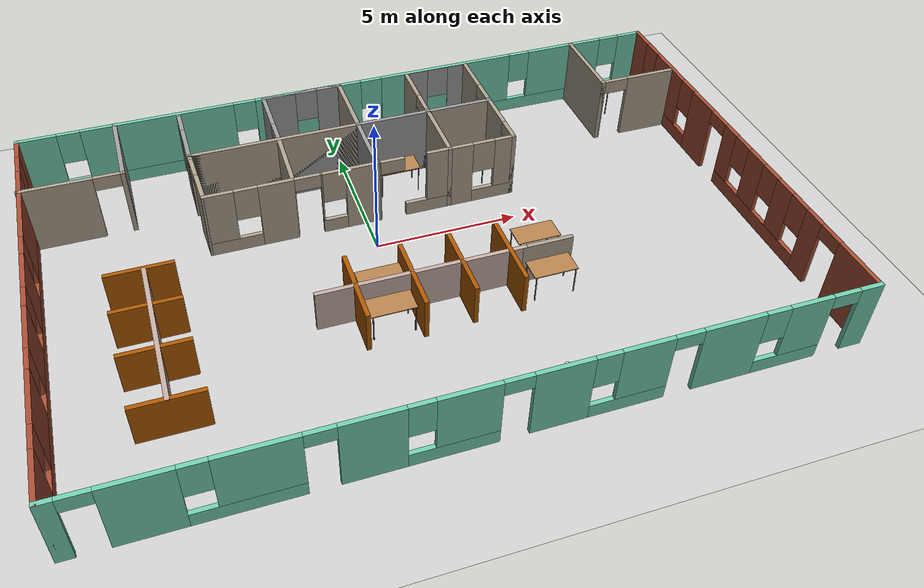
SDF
<sdf version="1.6">
 <world name="default">
  <light name="sun" type="directional">
   <pose>0 0 10 0 -0 0</pose>
   <diffuse>0.8 0.8 0.8 1</diffuse>
   <specular>0.2 0.2 0.2 1</specular>
   <attenuation>
    <range>1000</range>
    <constant>0.9</constant>
    <linear>0.01</linear>
    <quadratic>0.001</quadratic>
   </attenuation>
   <direction>-0.5 0.1 -0.9</direction>
  </light>
  <model name="ground_plane">
   <static>1</static>
   <link name="link">
    <collision name="collision">
     <geometry><plane><normal>0 0 1</normal><size>100 100</size></plane></geometry>
     <surface>
      <contact><collide_bitmask>65535</collide_bitmask></contact>
      <friction><ode><mu>100</mu><mu2>50</mu2></ode></friction>
     </surface>
    </collision>
    <visual name="visual">
     <cast_shadows>0</cast_shadows>
     <geometry><plane><normal>0 0 1</normal><size>100 100</size></plane></geometry>
     <material>
      <script><uri>file://media/materials/scripts/gazebo.material</uri><name>Gazebo/Grey</name></script>
     </material>
    </visual>
   </link>
  </model>
  <gravity>0 0 -9.8</gravity>
  <magnetic_field>6e-06 2.3e-05 -4.2e-05</magnetic_field>
  <atmosphere type="adiabatic"/>
  <physics name="default_physics" default="0" type="ode">
   <max_step_size>0.001</max_step_size>
   <real_time_factor>1</real_time_factor>
   <real_time_update_rate>1000</real_time_update_rate>
  </physics>
  <scene><ambient>0.4 0.4 0.4 1</ambient><background>0.7 0.7 0.7 1</background><shadows>1</shadows></scene>
  <spherical_coordinates>
   <surface_model>EARTH_WGS84</surface_model>
   <latitude_deg>0</latitude_deg>
   <longitude_deg>0</longitude_deg>
   <elevation>0</elevation>
   <heading_deg>0</heading_deg>
  </spherical_coordinates>
  <model name="officespace">
   <pose>0.84701 -1.22405 0 0 -0 0</pose>
   <link name="Wall_10">
    <pose>0.019 7.5445 0 0 -0 3.14159</pose>
    <visual name="Wall_10_Visual_0">
     <pose>-11.5075 0 1.25 0 -0 0</pose>
     <geometry><box><size>0.985001 0.15 2.5</size></box></geometry>
     <material>
      <script><uri>file://media/materials/scripts/gazebo.material</uri><name>Gazebo/Grey</name></script>
      <ambient>0.435294 0.796078 0.67451 1</ambient>
     </material>
     <meta><layer>0</layer></meta>
    </visual>
    <collision name="Wall_10_Collision_0">
     <geometry><box><size>0.985001 0.15 2.5</size></box></geometry>
     <pose>-11.5075 0 1.25 0 -0 0</pose>
    </collision>
    <visual name="Wall_10_Visual_1">
     <pose>0.492501 0 0.25 0 -0 0</pose>
     <geometry><box><size>23.015 0.15 0.5</size></box></geometry>
     <material>
      <script><uri>file://media/materials/scripts/gazebo.material</uri><name>Gazebo/Grey</name></script>
      <ambient>0.435294 0.796078 0.67451 1</ambient>
     </material>
     <meta><layer>0</layer></meta>
    </visual>
    <collision name="Wall_10_Collision_1">
     <geometry><box><size>23.015 0.15 0.5</size></box></geometry>
     <pose>0.492501 0 0.25 0 -0 0</pose>
    </collision>
    <visual name="Wall_10_Visual_2">
     <pose>-8.6945 0 1.5 0 -0 0</pose>
     <geometry><box><size>3.041 0.15 2</size></box></geometry>
     <material>
      <script><uri>file://media/materials/scripts/gazebo.material</uri><name>Gazebo/Grey</name></script>
      <ambient>0.435294 0.796078 0.67451 1</ambient>
     </material>
     <meta><layer>0</layer></meta>
    </visual>
    <collision name="Wall_10_Collision_2">
     <geometry><box><size>3.041 0.15 2</size></box></geometry>
     <pose>-8.6945 0 1.5 0 -0 0</pose>
    </collision>
    <visual name="Wall_10_Visual_3">
     <pose>-3.784 0 1.5 0 -0 0</pose>
     <geometry><box><size>5.18 0.15 2</size></box></geometry>
     <material>
      <script><uri>file://media/materials/scripts/gazebo.material</uri><name>Gazebo/Grey</name></script>
      <ambient>0.435294 0.796078 0.67451 1</ambient>
     </material>
     <meta><layer>0</layer></meta>
    </visual>
    <collision name="Wall_10_Collision_3">
     <geometry><box><size>5.18 0.15 2</size></box></geometry>
     <pose>-3.784 0 1.5 0 -0 0</pose>
    </collision>
    <visual name="Wall_10_Visual_4">
     <pose>1.598 0 1.5 0 -0 0</pose>
     <geometry><box><size>3.984 0.15 2</size></box></geometry>
     <material>
      <script><uri>file://media/materials/scripts/gazebo.material</uri><name>Gazebo/Grey</name></script>
      <ambient>0.435294 0.796078 0.67451 1</ambient>
     </material>
     <meta><layer>0</layer></meta>
    </visual>
    <collision name="Wall_10_Collision_4">
     <geometry><box><size>3.984 0.15 2</size></box></geometry>
     <pose>1.598 0 1.5 0 -0 0</pose>
    </collision>
    <visual name="Wall_10_Visual_5">
     <pose>7.095 0 1.5 0 -0 0</pose>
     <geometry><box><size>5.41 0.15 2</size></box></geometry>
     <material>
      <script><uri>file://media/materials/scripts/gazebo.material</uri><name>Gazebo/Grey</name></script>
      <ambient>0.435294 0.796078 0.67451 1</ambient>
     </material>
     <meta><layer>0</layer></meta>
    </visual>
    <collision name="Wall_10_Collision_5">
     <geometry><box><size>5.41 0.15 2</size></box></geometry>
     <pose>7.095 0 1.5 0 -0 0</pose>
    </collision>
    <visual name="Wall_10_Visual_6">
     <pose>11.3 0 1.5 0 -0 0</pose>
     <geometry><box><size>1.4 0.15 2</size></box></geometry>
     <material>
      <script><uri>file://media/materials/scripts/gazebo.material</uri><name>Gazebo/Grey</name></script>
      <ambient>0.435294 0.796078 0.67451 1</ambient>
     </material>
     <meta><layer>0</layer></meta>
    </visual>
    <collision name="Wall_10_Collision_6">
     <geometry><box><size>1.4 0.15 2</size></box></geometry>
     <pose>11.3 0 1.5 0 -0 0</pose>
    </collision>
    <visual name="Wall_10_Visual_7">
     <pose>-10.615 0 1.9 0 -0 0</pose>
     <geometry><box><size>0.8 0.15 1.2</size></box></geometry>
     <material>
      <script><uri>file://media/materials/scripts/gazebo.material</uri><name>Gazebo/Grey</name></script>
      <ambient>0.435294 0.796078 0.67451 1</ambient>
     </material>
     <meta><layer>0</layer></meta>
    </visual>
    <collision name="Wall_10_Collision_7">
     <geometry><box><size>0.8 0.15 1.2</size></box></geometry>
     <pose>-10.615 0 1.9 0 -0 0</pose>
    </collision>
    <visual name="Wall_10_Visual_8">
     <pose>-6.774 0 1.9 0 -0 0</pose>
     <geometry><box><size>0.8 0.15 1.2</size></box></geometry>
     <material>
      <script><uri>file://media/materials/scripts/gazebo.material</uri><name>Gazebo/Grey</name></script>
      <ambient>0.435294 0.796078 0.67451 1</ambient>
     </material>
     <meta><layer>0</layer></meta>
    </visual>
    <collision name="Wall_10_Collision_8">
     <geometry><box><size>0.8 0.15 1.2</size></box></geometry>
     <pose>-6.774 0 1.9 0 -0 0</pose>
    </collision>
    <visual name="Wall_10_Visual_9">
     <pose>-0.794 0 1.9 0 -0 0</pose>
     <geometry><box><size>0.8 0.15 1.2</size></box></geometry>
     <material>
      <script><uri>file://media/materials/scripts/gazebo.material</uri><name>Gazebo/Grey</name></script>
      <ambient>0.435294 0.796078 0.67451 1</ambient>
     </material>
     <meta><layer>0</layer></meta>
    </visual>
    <collision name="Wall_10_Collision_9">
     <geometry><box><size>0.8 0.15 1.2</size></box></geometry>
     <pose>-0.794 0 1.9 0 -0 0</pose>
    </collision>
    <visual name="Wall_10_Visual_10">
     <pose>3.99 0 1.9 0 -0 0</pose>
     <geometry><box><size>0.8 0.15 1.2</size></box></geometry>
     <material>
      <script><uri>file://media/materials/scripts/gazebo.material</uri><name>Gazebo/Grey</name></script>
      <ambient>0.435294 0.796078 0.67451 1</ambient>
     </material>
     <meta><layer>0</layer></meta>
    </visual>
    <collision name="Wall_10_Collision_10">
     <geometry><box><size>0.8 0.15 1.2</size></box></geometry>
     <pose>3.99 0 1.9 0 -0 0</pose>
    </collision>
    <visual name="Wall_10_Visual_11">
     <pose>10.2 0 1.9 0 -0 0</pose>
     <geometry><box><size>0.8 0.15 1.2</size></box></geometry>
     <material>
      <script><uri>file://media/materials/scripts/gazebo.material</uri><name>Gazebo/Grey</name></script>
      <ambient>0.435294 0.796078 0.67451 1</ambient>
     </material>
     <meta><layer>0</layer></meta>
    </visual>
    <collision name="Wall_10_Collision_11">
     <geometry><box><size>0.8 0.15 1.2</size></box></geometry>
     <pose>10.2 0 1.9 0 -0 0</pose>
    </collision>
   </link>
   <link name="Wall_11">
    <pose>-11.906 -0.005499 0 0 0 -1.5708</pose>
    <visual name="Wall_11_Visual_0">
     <pose>-7.1375 0 1.25 0 -0 0</pose>
     <geometry><box><size>0.975 0.15 2.5</size></box></geometry>
     <material>
      <script><uri>file://media/materials/scripts/gazebo.material</uri><name>Gazebo/Bricks</name></script>
      <ambient>0.435294 0.796078 0.67451 1</ambient>
     </material>
     <meta><layer>0</layer></meta>
    </visual>
    <collision name="Wall_11_Collision_0">
     <geometry><box><size>0.975 0.15 2.5</size></box></geometry>
     <pose>-7.1375 0 1.25 0 -0 0</pose>
    </collision>
    <visual name="Wall_11_Visual_1">
     <pose>0.4875 0 0.25 0 -0 0</pose>
     <geometry><box><size>14.275 0.15 0.5</size></box></geometry>
     <material>
      <script><uri>file://media/materials/scripts/gazebo.material</uri><name>Gazebo/Bricks</name></script>
      <ambient>0.435294 0.796078 0.67451 1</ambient>
     </material>
     <meta><layer>0</layer></meta>
    </visual>
    <collision name="Wall_11_Collision_1">
     <geometry><box><size>14.275 0.15 0.5</size></box></geometry>
     <pose>0.4875 0 0.25 0 -0 0</pose>
    </collision>
    <visual name="Wall_11_Visual_2">
     <pose>-4.134 0 1.5 0 -0 0</pose>
     <geometry><box><size>3.432 0.15 2</size></box></geometry>
     <material>
      <script><uri>file://media/materials/scripts/gazebo.material</uri><name>Gazebo/Bricks</name></script>
      <ambient>0.435294 0.796078 0.67451 1</ambient>
     </material>
     <meta><layer>0</layer></meta>
    </visual>
    <collision name="Wall_11_Collision_2">
     <geometry><box><size>3.432 0.15 2</size></box></geometry>
     <pose>-4.134 0 1.5 0 -0 0</pose>
    </collision>
    <visual name="Wall_11_Visual_3">
     <pose>-0.868 0 1.5 0 -0 0</pose>
     <geometry><box><size>1.5 0.15 2</size></box></geometry>
     <material>
      <script><uri>file://media/materials/scripts/gazebo.material</uri><name>Gazebo/Bricks</name></script>
      <ambient>0.435294 0.796078 0.67451 1</ambient>
     </material>
     <meta><layer>0</layer></meta>
    </visual>
    <collision name="Wall_11_Collision_3">
     <geometry><box><size>1.5 0.15 2</size></box></geometry>
     <pose>-0.868 0 1.5 0 -0 0</pose>
    </collision>
    <visual name="Wall_11_Visual_4">
     <pose>1.524 0 1.5 0 -0 0</pose>
     <geometry><box><size>1.684 0.15 2</size></box></geometry>
     <material>
      <script><uri>file://media/materials/scripts/gazebo.material</uri><name>Gazebo/Bricks</name></script>
      <ambient>0.435294 0.796078 0.67451 1</ambient>
     </material>
     <meta><layer>0</layer></meta>
    </visual>
    <collision name="Wall_11_Collision_4">
     <geometry><box><size>1.684 0.15 2</size></box></geometry>
     <pose>1.524 0 1.5 0 -0 0</pose>
    </collision>
    <visual name="Wall_11_Visual_5">
     <pose>4.123 0 1.5 0 -0 0</pose>
     <geometry><box><size>1.914 0.15 2</size></box></geometry>
     <material>
      <script><uri>file://media/materials/scripts/gazebo.material</uri><name>Gazebo/Bricks</name></script>
      <ambient>0.435294 0.796078 0.67451 1</ambient>
     </material>
     <meta><layer>0</layer></meta>
    </visual>
    <collision name="Wall_11_Collision_5">
     <geometry><box><size>1.914 0.15 2</size></box></geometry>
     <pose>4.123 0 1.5 0 -0 0</pose>
    </collision>
    <visual name="Wall_11_Visual_6">
     <pose>6.7525 0 1.5 0 -0 0</pose>
     <geometry><box><size>1.745 0.15 2</size></box></geometry>
     <material>
      <script><uri>file://media/materials/scripts/gazebo.material</uri><name>Gazebo/Bricks</name></script>
      <ambient>0.435294 0.796078 0.67451 1</ambient>
     </material>
     <meta><layer>0</layer></meta>
    </visual>
    <collision name="Wall_11_Collision_6">
     <geometry><box><size>1.745 0.15 2</size></box></geometry>
     <pose>6.7525 0 1.5 0 -0 0</pose>
    </collision>
    <visual name="Wall_11_Visual_7">
     <pose>-6.25 0 1.9 0 -0 0</pose>
     <geometry><box><size>0.8 0.15 1.2</size></box></geometry>
     <material>
      <script><uri>file://media/materials/scripts/gazebo.material</uri><name>Gazebo/Bricks</name></script>
      <ambient>0.435294 0.796078 0.67451 1</ambient>
     </material>
     <meta><layer>0</layer></meta>
    </visual>
    <collision name="Wall_11_Collision_7">
     <geometry><box><size>0.8 0.15 1.2</size></box></geometry>
     <pose>-6.25 0 1.9 0 -0 0</pose>
    </collision>
    <visual name="Wall_11_Visual_8">
     <pose>-2.018 0 1.9 0 -0 0</pose>
     <geometry><box><size>0.8 0.15 1.2</size></box></geometry>
     <material>
      <script><uri>file://media/materials/scripts/gazebo.material</uri><name>Gazebo/Bricks</name></script>
      <ambient>0.435294 0.796078 0.67451 1</ambient>
     </material>
     <meta><layer>0</layer></meta>
    </visual>
    <collision name="Wall_11_Collision_8">
     <geometry><box><size>0.8 0.15 1.2</size></box></geometry>
     <pose>-2.018 0 1.9 0 -0 0</pose>
    </collision>
    <visual name="Wall_11_Visual_9">
     <pose>0.282 0 1.9 0 -0 0</pose>
     <geometry><box><size>0.8 0.15 1.2</size></box></geometry>
     <material>
      <script><uri>file://media/materials/scripts/gazebo.material</uri><name>Gazebo/Bricks</name></script>
      <ambient>0.435294 0.796078 0.67451 1</ambient>
     </material>
     <meta><layer>0</layer></meta>
    </visual>
    <collision name="Wall_11_Collision_9">
     <geometry><box><size>0.8 0.15 1.2</size></box></geometry>
     <pose>0.282 0 1.9 0 -0 0</pose>
    </collision>
    <visual name="Wall_11_Visual_10">
     <pose>2.766 0 1.9 0 -0 0</pose>
     <geometry><box><size>0.8 0.15 1.2</size></box></geometry>
     <material>
      <script><uri>file://media/materials/scripts/gazebo.material</uri><name>Gazebo/Bricks</name></script>
      <ambient>0.435294 0.796078 0.67451 1</ambient>
     </material>
     <meta><layer>0</layer></meta>
    </visual>
    <collision name="Wall_11_Collision_10">
     <geometry><box><size>0.8 0.15 1.2</size></box></geometry>
     <pose>2.766 0 1.9 0 -0 0</pose>
    </collision>
    <visual name="Wall_11_Visual_11">
     <pose>5.48 0 1.9 0 -0 0</pose>
     <geometry><box><size>0.8 0.15 1.2</size></box></geometry>
     <material>
      <script><uri>file://media/materials/scripts/gazebo.material</uri><name>Gazebo/Bricks</name></script>
      <ambient>0.435294 0.796078 0.67451 1</ambient>
     </material>
     <meta><layer>0</layer></meta>
    </visual>
    <collision name="Wall_11_Collision_11">
     <geometry><box><size>0.8 0.15 1.2</size></box></geometry>
     <pose>5.48 0 1.9 0 -0 0</pose>
    </collision>
   </link>
   <link name="Wall_13">
    <collision name="Wall_13_Collision">
     <geometry><box><size>3 0.15 2.5</size></box></geometry>
     <pose>0 0 1.25 0 -0 0</pose>
    </collision>
    <visual name="Wall_13_Visual">
     <pose>0 0 1.25 0 -0 0</pose>
     <geometry><box><size>3 0.15 2.5</size></box></geometry>
     <material>
      <script><uri>file://media/materials/scripts/gazebo.material</uri><name>Gazebo/Grey</name></script>
      <ambient>1 1 1 1</ambient>
     </material>
     <meta><layer>0</layer></meta>
    </visual>
    <pose>-8.594 6.1305 0 0 0 -1.5708</pose>
   </link>
   <link name="Wall_14">
    <pose>-10.269 4.7055 0 0 -0 3.14159</pose>
    <visual name="Wall_14_Visual_0">
     <pose>-1.673 0 1.25 0 -0 0</pose>
     <geometry><box><size>0.154 0.15 2.5</size></box></geometry>
     <material>
      <script><uri>file://media/materials/scripts/gazebo.material</uri><name>Gazebo/Grey</name></script>
      <ambient>0.666667 0.623529 0.54902 1</ambient>
     </material>
     <meta><layer>0</layer></meta>
    </visual>
    <collision name="Wall_14_Collision_0">
     <geometry><box><size>0.154 0.15 2.5</size></box></geometry>
     <pose>-1.673 0 1.25 0 -0 0</pose>
    </collision>
    <visual name="Wall_14_Visual_1">
     <pose>0.527 0 1.25 0 -0 0</pose>
     <geometry><box><size>2.446 0.15 2.5</size></box></geometry>
     <material>
      <script><uri>file://media/materials/scripts/gazebo.material</uri><name>Gazebo/Grey</name></script>
      <ambient>0.666667 0.623529 0.54902 1</ambient>
     </material>
     <meta><layer>0</layer></meta>
    </visual>
    <collision name="Wall_14_Collision_1">
     <geometry><box><size>2.446 0.15 2.5</size></box></geometry>
     <pose>0.527 0 1.25 0 -0 0</pose>
    </collision>
    <visual name="Wall_14_Visual_2">
     <pose>-1.146 0 2.25 0 -0 0</pose>
     <geometry><box><size>0.9 0.15 0.5</size></box></geometry>
     <material>
      <script><uri>file://media/materials/scripts/gazebo.material</uri><name>Gazebo/Grey</name></script>
      <ambient>0.666667 0.623529 0.54902 1</ambient>
     </material>
     <meta><layer>0</layer></meta>
    </visual>
    <collision name="Wall_14_Collision_2">
     <geometry><box><size>0.9 0.15 0.5</size></box></geometry>
     <pose>-1.146 0 2.25 0 -0 0</pose>
    </collision>
   </link>
   <link name="Wall_16">
    <collision name="Wall_16_Collision">
     <geometry><box><size>3 0.15 2.5</size></box></geometry>
     <pose>0 0 1.25 0 -0 0</pose>
    </collision>
    <visual name="Wall_16_Visual">
     <pose>0 0 1.25 0 -0 0</pose>
     <geometry><box><size>3 0.15 2.5</size></box></geometry>
     <material>
      <script><uri>file://media/materials/scripts/gazebo.material</uri><name>Gazebo/Grey</name></script>
      <ambient>0.666667 0.623529 0.54902 1</ambient>
     </material>
     <meta><layer>0</layer></meta>
    </visual>
    <pose>9.001 6.1075 0 0 0 -1.5708</pose>
   </link>
   <link name="Wall_17">
    <pose>10.426 4.6825 0 0 -0 0</pose>
    <visual name="Wall_17_Visual_0">
     <pose>-1.4115 0 1.25 0 -0 0</pose>
     <geometry><box><size>0.176999 0.15 2.5</size></box></geometry>
     <material>
      <script><uri>file://media/materials/scripts/gazebo.material</uri><name>Gazebo/Grey</name></script>
      <ambient>0.666667 0.623529 0.54902 1</ambient>
     </material>
     <meta><layer>0</layer></meta>
    </visual>
    <collision name="Wall_17_Collision_0">
     <geometry><box><size>0.176999 0.15 2.5</size></box></geometry>
     <pose>-1.4115 0 1.25 0 -0 0</pose>
    </collision>
    <visual name="Wall_17_Visual_1">
     <pose>0.538499 0 1.25 0 -0 0</pose>
     <geometry><box><size>1.923 0.15 2.5</size></box></geometry>
     <material>
      <script><uri>file://media/materials/scripts/gazebo.material</uri><name>Gazebo/Grey</name></script>
      <ambient>0.666667 0.623529 0.54902 1</ambient>
     </material>
     <meta><layer>0</layer></meta>
    </visual>
    <collision name="Wall_17_Collision_1">
     <geometry><box><size>1.923 0.15 2.5</size></box></geometry>
     <pose>0.538499 0 1.25 0 -0 0</pose>
    </collision>
    <visual name="Wall_17_Visual_2">
     <pose>-0.873001 0 2.25 0 -0 0</pose>
     <geometry><box><size>0.9 0.15 0.5</size></box></geometry>
     <material>
      <script><uri>file://media/materials/scripts/gazebo.material</uri><name>Gazebo/Grey</name></script>
      <ambient>0.666667 0.623529 0.54902 1</ambient>
     </material>
     <meta><layer>0</layer></meta>
    </visual>
    <collision name="Wall_17_Collision_2">
     <geometry><box><size>0.9 0.15 0.5</size></box></geometry>
     <pose>-0.873001 0 2.25 0 -0 0</pose>
    </collision>
   </link>
   <link name="Wall_19">
    <pose>-6.363 6.2325 0 0 0 -1.5708</pose>
    <visual name="Wall_19_Visual_0">
     <pose>-1.2635 0 1.25 0 -0 0</pose>
     <geometry><box><size>0.223 0.15 2.5</size></box></geometry>
     <material>
      <script><uri>file://media/materials/scripts/gazebo.material</uri><name>Gazebo/Grey</name></script>
      <ambient>1 1 1 1</ambient>
     </material>
     <meta><layer>0</layer></meta>
    </visual>
    <collision name="Wall_19_Collision_0">
     <geometry><box><size>0.223 0.15 2.5</size></box></geometry>
     <pose>-1.2635 0 1.25 0 -0 0</pose>
    </collision>
    <visual name="Wall_19_Visual_1">
     <pose>0.5615 0 1.25 0 -0 0</pose>
     <geometry><box><size>1.627 0.15 2.5</size></box></geometry>
     <material>
      <script><uri>file://media/materials/scripts/gazebo.material</uri><name>Gazebo/Grey</name></script>
      <ambient>1 1 1 1</ambient>
     </material>
     <meta><layer>0</layer></meta>
    </visual>
    <collision name="Wall_19_Collision_1">
     <geometry><box><size>1.627 0.15 2.5</size></box></geometry>
     <pose>0.5615 0 1.25 0 -0 0</pose>
    </collision>
    <visual name="Wall_19_Visual_2">
     <pose>-0.702 0 2.25 0 -0 0</pose>
     <geometry><box><size>0.9 0.15 0.5</size></box></geometry>
     <material>
      <script><uri>file://media/materials/scripts/gazebo.material</uri><name>Gazebo/Grey</name></script>
      <ambient>1 1 1 1</ambient>
     </material>
     <meta><layer>0</layer></meta>
    </visual>
    <collision name="Wall_19_Collision_2">
     <geometry><box><size>0.9 0.15 0.5</size></box></geometry>
     <pose>-0.702 0 2.25 0 -0 0</pose>
    </collision>
   </link>
   <link name="Wall_20">
    <collision name="Wall_20_Collision">
     <geometry><box><size>3.25 0.15 2.5</size></box></geometry>
     <pose>0 0 1.25 0 -0 0</pose>
    </collision>
    <visual name="Wall_20_Visual">
     <pose>0 0 1.25 0 -0 0</pose>
     <geometry><box><size>3.25 0.15 2.5</size></box></geometry>
     <material>
      <script><uri>file://media/materials/scripts/gazebo.material</uri><name>Gazebo/Grey</name></script>
      <ambient>1 1 1 1</ambient>
     </material>
     <meta><layer>0</layer></meta>
    </visual>
    <pose>-4.813 4.9325 0 0 -0 0</pose>
   </link>
   <link name="Wall_21">
    <pose>-3.263 6.2325 0 0 -0 1.5708</pose>
    <visual name="Wall_21_Visual_0">
     <pose>-1.3205 0 1.25 0 -0 0</pose>
     <geometry><box><size>0.109 0.15 2.5</size></box></geometry>
     <material>
      <script><uri>file://media/materials/scripts/gazebo.material</uri><name>Gazebo/Grey</name></script>
      <ambient>1 1 1 1</ambient>
     </material>
     <meta><layer>0</layer></meta>
    </visual>
    <collision name="Wall_21_Collision_0">
     <geometry><box><size>0.109 0.15 2.5</size></box></geometry>
     <pose>-1.3205 0 1.25 0 -0 0</pose>
    </collision>
    <visual name="Wall_21_Visual_1">
     <pose>0.5045 0 1.25 0 -0 0</pose>
     <geometry><box><size>1.741 0.15 2.5</size></box></geometry>
     <material>
      <script><uri>file://media/materials/scripts/gazebo.material</uri><name>Gazebo/Grey</name></script>
      <ambient>1 1 1 1</ambient>
     </material>
     <meta><layer>0</layer></meta>
    </visual>
    <collision name="Wall_21_Collision_1">
     <geometry><box><size>1.741 0.15 2.5</size></box></geometry>
     <pose>0.5045 0 1.25 0 -0 0</pose>
    </collision>
    <visual name="Wall_21_Visual_2">
     <pose>-0.816 0 2.25 0 -0 0</pose>
     <geometry><box><size>0.9 0.15 0.5</size></box></geometry>
     <material>
      <script><uri>file://media/materials/scripts/gazebo.material</uri><name>Gazebo/Grey</name></script>
      <ambient>1 1 1 1</ambient>
     </material>
     <meta><layer>0</layer></meta>
    </visual>
    <collision name="Wall_21_Collision_2">
     <geometry><box><size>0.9 0.15 0.5</size></box></geometry>
     <pose>-0.816 0 2.25 0 -0 0</pose>
    </collision>
   </link>
   <link name="Wall_22">
    <pose>-1.838 7.5325 0 0 -0 0</pose>
    <visual name="Wall_22_Visual_0">
     <pose>-0.878 0 1.25 0 -0 0</pose>
     <geometry><box><size>1.244 0.15 2.5</size></box></geometry>
     <material>
      <script><uri>file://media/materials/scripts/gazebo.material</uri><name>Gazebo/Grey</name></script>
      <ambient>1 1 1 1</ambient>
     </material>
     <meta><layer>0</layer></meta>
    </visual>
    <collision name="Wall_22_Collision_0">
     <geometry><box><size>1.244 0.15 2.5</size></box></geometry>
     <pose>-0.878 0 1.25 0 -0 0</pose>
    </collision>
    <visual name="Wall_22_Visual_1">
     <pose>0.622 0 0.25 0 -0 0</pose>
     <geometry><box><size>1.756 0.15 0.5</size></box></geometry>
     <material>
      <script><uri>file://media/materials/scripts/gazebo.material</uri><name>Gazebo/Grey</name></script>
      <ambient>1 1 1 1</ambient>
     </material>
     <meta><layer>0</layer></meta>
    </visual>
    <collision name="Wall_22_Collision_1">
     <geometry><box><size>1.756 0.15 0.5</size></box></geometry>
     <pose>0.622 0 0.25 0 -0 0</pose>
    </collision>
    <visual name="Wall_22_Visual_2">
     <pose>1.022 0 1.5 0 -0 0</pose>
     <geometry><box><size>0.956 0.15 2</size></box></geometry>
     <material>
      <script><uri>file://media/materials/scripts/gazebo.material</uri><name>Gazebo/Grey</name></script>
      <ambient>1 1 1 1</ambient>
     </material>
     <meta><layer>0</layer></meta>
    </visual>
    <collision name="Wall_22_Collision_2">
     <geometry><box><size>0.956 0.15 2</size></box></geometry>
     <pose>1.022 0 1.5 0 -0 0</pose>
    </collision>
    <visual name="Wall_22_Visual_3">
     <pose>0.144 0 1.9 0 -0 0</pose>
     <geometry><box><size>0.8 0.15 1.2</size></box></geometry>
     <material>
      <script><uri>file://media/materials/scripts/gazebo.material</uri><name>Gazebo/Grey</name></script>
      <ambient>1 1 1 1</ambient>
     </material>
     <meta><layer>0</layer></meta>
    </visual>
    <collision name="Wall_22_Collision_3">
     <geometry><box><size>0.8 0.15 1.2</size></box></geometry>
     <pose>0.144 0 1.9 0 -0 0</pose>
    </collision>
   </link>
   <link name="Wall_23">
    <collision name="Wall_23_Collision">
     <geometry><box><size>2.75 0.15 2.5</size></box></geometry>
     <pose>0 0 1.25 0 -0 0</pose>
    </collision>
    <visual name="Wall_23_Visual">
     <pose>0 0 1.25 0 -0 0</pose>
     <geometry><box><size>2.75 0.15 2.5</size></box></geometry>
     <material>
      <script><uri>file://media/materials/scripts/gazebo.material</uri><name>Gazebo/Grey</name></script>
      <ambient>0.666667 0.623529 0.54902 1</ambient>
     </material>
     <meta><layer>0</layer></meta>
    </visual>
    <pose>-0.413001 6.2325 0 0 0 -1.5708</pose>
   </link>
   <link name="Wall_24">
    <collision name="Wall_24_Collision">
     <geometry><box><size>2.75 0.15 2.5</size></box></geometry>
     <pose>0 0 1.25 0 -0 0</pose>
    </collision>
    <visual name="Wall_24_Visual">
     <pose>0 0 1.25 0 -0 0</pose>
     <geometry><box><size>2.75 0.15 2.5</size></box></geometry>
     <material>
      <script><uri>file://media/materials/scripts/gazebo.material</uri><name>Gazebo/Grey</name></script>
      <ambient>1 1 1 1</ambient>
     </material>
     <meta><layer>0</layer></meta>
    </visual>
    <pose>0.887 4.9325 0 0 -0 0</pose>
   </link>
   <link name="Wall_25">
    <collision name="Wall_25_Collision">
     <geometry><box><size>2.5 0.15 2.5</size></box></geometry>
     <pose>0 0 1.25 0 -0 0</pose>
    </collision>
    <visual name="Wall_25_Visual">
     <pose>0 0 1.25 0 -0 0</pose>
     <geometry><box><size>2.5 0.15 2.5</size></box></geometry>
     <material>
      <script><uri>file://media/materials/scripts/gazebo.material</uri><name>Gazebo/Grey</name></script>
      <ambient>1 1 1 1</ambient>
     </material>
     <meta><layer>0</layer></meta>
    </visual>
    <pose>3.362 4.9325 0 0 -0 0</pose>
   </link>
   <link name="Wall_26">
    <pose>4.537 6.2325 0 0 -0 1.5708</pose>
    <visual name="Wall_26_Visual_0">
     <pose>-1.2745 0 1.25 0 -0 0</pose>
     <geometry><box><size>0.201 0.15 2.5</size></box></geometry>
     <material>
      <script><uri>file://media/materials/scripts/gazebo.material</uri><name>Gazebo/Grey</name></script>
      <ambient>0.666667 0.623529 0.54902 1</ambient>
     </material>
     <meta><layer>0</layer></meta>
    </visual>
    <collision name="Wall_26_Collision_0">
     <geometry><box><size>0.201 0.15 2.5</size></box></geometry>
     <pose>-1.2745 0 1.25 0 -0 0</pose>
    </collision>
    <visual name="Wall_26_Visual_1">
     <pose>0.5505 0 1.25 0 -0 0</pose>
     <geometry><box><size>1.649 0.15 2.5</size></box></geometry>
     <material>
      <script><uri>file://media/materials/scripts/gazebo.material</uri><name>Gazebo/Grey</name></script>
      <ambient>0.666667 0.623529 0.54902 1</ambient>
     </material>
     <meta><layer>0</layer></meta>
    </visual>
    <collision name="Wall_26_Collision_1">
     <geometry><box><size>1.649 0.15 2.5</size></box></geometry>
     <pose>0.5505 0 1.25 0 -0 0</pose>
    </collision>
    <visual name="Wall_26_Visual_2">
     <pose>-0.724 0 2.25 0 -0 0</pose>
     <geometry><box><size>0.9 0.15 0.5</size></box></geometry>
     <material>
      <script><uri>file://media/materials/scripts/gazebo.material</uri><name>Gazebo/Grey</name></script>
      <ambient>0.666667 0.623529 0.54902 1</ambient>
     </material>
     <meta><layer>0</layer></meta>
    </visual>
    <collision name="Wall_26_Collision_2">
     <geometry><box><size>0.9 0.15 0.5</size></box></geometry>
     <pose>-0.724 0 2.25 0 -0 0</pose>
    </collision>
   </link>
   <link name="Wall_27">
    <pose>3.362 7.5325 0 0 -0 3.14159</pose>
    <visual name="Wall_27_Visual_0">
     <pose>-0.8615 0 1.25 0 -0 0</pose>
     <geometry><box><size>0.777 0.15 2.5</size></box></geometry>
     <material>
      <script><uri>file://media/materials/scripts/gazebo.material</uri><name>Gazebo/Grey</name></script>
      <ambient>1 1 1 1</ambient>
     </material>
     <meta><layer>0</layer></meta>
    </visual>
    <collision name="Wall_27_Collision_0">
     <geometry><box><size>0.777 0.15 2.5</size></box></geometry>
     <pose>-0.8615 0 1.25 0 -0 0</pose>
    </collision>
    <visual name="Wall_27_Visual_1">
     <pose>0.3885 0 0.25 0 -0 0</pose>
     <geometry><box><size>1.723 0.15 0.5</size></box></geometry>
     <material>
      <script><uri>file://media/materials/scripts/gazebo.material</uri><name>Gazebo/Grey</name></script>
      <ambient>1 1 1 1</ambient>
     </material>
     <meta><layer>0</layer></meta>
    </visual>
    <collision name="Wall_27_Collision_1">
     <geometry><box><size>1.723 0.15 0.5</size></box></geometry>
     <pose>0.3885 0 0.25 0 -0 0</pose>
    </collision>
    <visual name="Wall_27_Visual_2">
     <pose>0.7885 0 1.5 0 -0 0</pose>
     <geometry><box><size>0.923 0.15 2</size></box></geometry>
     <material>
      <script><uri>file://media/materials/scripts/gazebo.material</uri><name>Gazebo/Grey</name></script>
      <ambient>1 1 1 1</ambient>
     </material>
     <meta><layer>0</layer></meta>
    </visual>
    <collision name="Wall_27_Collision_2">
     <geometry><box><size>0.923 0.15 2</size></box></geometry>
     <pose>0.7885 0 1.5 0 -0 0</pose>
    </collision>
    <visual name="Wall_27_Visual_3">
     <pose>-0.073 0 1.9 0 -0 0</pose>
     <geometry><box><size>0.8 0.15 1.2</size></box></geometry>
     <material>
      <script><uri>file://media/materials/scripts/gazebo.material</uri><name>Gazebo/Grey</name></script>
      <ambient>1 1 1 1</ambient>
     </material>
     <meta><layer>0</layer></meta>
    </visual>
    <collision name="Wall_27_Collision_3">
     <geometry><box><size>0.8 0.15 1.2</size></box></geometry>
     <pose>-0.073 0 1.9 0 -0 0</pose>
    </collision>
   </link>
   <link name="Wall_28">
    <pose>2.187 6.2325 0 0 0 -1.5708</pose>
    <visual name="Wall_28_Visual_0">
     <pose>-0.5735 0 1.25 0 -0 0</pose>
     <geometry><box><size>1.603 0.15 2.5</size></box></geometry>
     <material>
      <script><uri>file://media/materials/scripts/gazebo.material</uri><name>Gazebo/Grey</name></script>
      <ambient>0.666667 0.623529 0.54902 1</ambient>
     </material>
     <meta><layer>0</layer></meta>
    </visual>
    <collision name="Wall_28_Collision_0">
     <geometry><box><size>1.603 0.15 2.5</size></box></geometry>
     <pose>-0.5735 0 1.25 0 -0 0</pose>
    </collision>
    <visual name="Wall_28_Visual_1">
     <pose>1.2515 0 1.25 0 -0 0</pose>
     <geometry><box><size>0.247 0.15 2.5</size></box></geometry>
     <material>
      <script><uri>file://media/materials/scripts/gazebo.material</uri><name>Gazebo/Grey</name></script>
      <ambient>0.666667 0.623529 0.54902 1</ambient>
     </material>
     <meta><layer>0</layer></meta>
    </visual>
    <collision name="Wall_28_Collision_1">
     <geometry><box><size>0.247 0.15 2.5</size></box></geometry>
     <pose>1.2515 0 1.25 0 -0 0</pose>
    </collision>
    <visual name="Wall_28_Visual_2">
     <pose>0.678 0 2.25 0 -0 0</pose>
     <geometry><box><size>0.9 0.15 0.5</size></box></geometry>
     <material>
      <script><uri>file://media/materials/scripts/gazebo.material</uri><name>Gazebo/Grey</name></script>
      <ambient>0.666667 0.623529 0.54902 1</ambient>
     </material>
     <meta><layer>0</layer></meta>
    </visual>
    <collision name="Wall_28_Collision_2">
     <geometry><box><size>0.9 0.15 0.5</size></box></geometry>
     <pose>0.678 0 2.25 0 -0 0</pose>
    </collision>
   </link>
   <link name="Wall_29">
    <collision name="Wall_29_Collision">
     <geometry><box><size>2.5 0.15 2.5</size></box></geometry>
     <pose>0 0 1.25 0 -0 0</pose>
    </collision>
    <visual name="Wall_29_Visual">
     <pose>0 0 1.25 0 -0 0</pose>
     <geometry><box><size>2.5 0.15 2.5</size></box></geometry>
     <material>
      <script><uri>file://media/materials/scripts/gazebo.material</uri><name>Gazebo/Grey</name></script>
      <ambient>0.666667 0.623529 0.54902 1</ambient>
     </material>
     <meta><layer>0</layer></meta>
    </visual>
    <pose>2.187 3.7575 0 0 0 -1.5708</pose>
   </link>
   <link name="Wall_30">
    <pose>3.362 2.5825 0 0 -0 0</pose>
    <visual name="Wall_30_Visual_0">
     <pose>-0.7885 0 1.25 0 -0 0</pose>
     <geometry><box><size>0.923 0.15 2.5</size></box></geometry>
     <material>
      <script><uri>file://media/materials/scripts/gazebo.material</uri><name>Gazebo/Grey</name></script>
      <ambient>0.666667 0.623529 0.54902 1</ambient>
     </material>
     <meta><layer>0</layer></meta>
    </visual>
    <collision name="Wall_30_Collision_0">
     <geometry><box><size>0.923 0.15 2.5</size></box></geometry>
     <pose>-0.7885 0 1.25 0 -0 0</pose>
    </collision>
    <visual name="Wall_30_Visual_1">
     <pose>0.4615 0 0.25 0 -0 0</pose>
     <geometry><box><size>1.577 0.15 0.5</size></box></geometry>
     <material>
      <script><uri>file://media/materials/scripts/gazebo.material</uri><name>Gazebo/Grey</name></script>
      <ambient>0.666667 0.623529 0.54902 1</ambient>
     </material>
     <meta><layer>0</layer></meta>
    </visual>
    <collision name="Wall_30_Collision_1">
     <geometry><box><size>1.577 0.15 0.5</size></box></geometry>
     <pose>0.4615 0 0.25 0 -0 0</pose>
    </collision>
    <visual name="Wall_30_Visual_2">
     <pose>0.8615 0 1.5 0 -0 0</pose>
     <geometry><box><size>0.777 0.15 2</size></box></geometry>
     <material>
      <script><uri>file://media/materials/scripts/gazebo.material</uri><name>Gazebo/Grey</name></script>
      <ambient>0.666667 0.623529 0.54902 1</ambient>
     </material>
     <meta><layer>0</layer></meta>
    </visual>
    <collision name="Wall_30_Collision_2">
     <geometry><box><size>0.777 0.15 2</size></box></geometry>
     <pose>0.8615 0 1.5 0 -0 0</pose>
    </collision>
    <visual name="Wall_30_Visual_3">
     <pose>0.073 0 1.9 0 -0 0</pose>
     <geometry><box><size>0.8 0.15 1.2</size></box></geometry>
     <material>
      <script><uri>file://media/materials/scripts/gazebo.material</uri><name>Gazebo/Grey</name></script>
      <ambient>0.666667 0.623529 0.54902 1</ambient>
     </material>
     <meta><layer>0</layer></meta>
    </visual>
    <collision name="Wall_30_Collision_3">
     <geometry><box><size>0.8 0.15 1.2</size></box></geometry>
     <pose>0.073 0 1.9 0 -0 0</pose>
    </collision>
   </link>
   <link name="Wall_31">
    <pose>4.537 3.7575 0 0 -0 1.5708</pose>
    <visual name="Wall_31_Visual_0">
     <pose>-1.2165 0 1.25 0 -0 0</pose>
     <geometry><box><size>0.067 0.15 2.5</size></box></geometry>
     <material>
      <script><uri>file://media/materials/scripts/gazebo.material</uri><name>Gazebo/Grey</name></script>
      <ambient>0.666667 0.623529 0.54902 1</ambient>
     </material>
     <meta><layer>0</layer></meta>
    </visual>
    <collision name="Wall_31_Collision_0">
     <geometry><box><size>0.067 0.15 2.5</size></box></geometry>
     <pose>-1.2165 0 1.25 0 -0 0</pose>
    </collision>
    <visual name="Wall_31_Visual_1">
     <pose>0.4835 0 1.25 0 -0 0</pose>
     <geometry><box><size>1.533 0.15 2.5</size></box></geometry>
     <material>
      <script><uri>file://media/materials/scripts/gazebo.material</uri><name>Gazebo/Grey</name></script>
      <ambient>0.666667 0.623529 0.54902 1</ambient>
     </material>
     <meta><layer>0</layer></meta>
    </visual>
    <collision name="Wall_31_Collision_1">
     <geometry><box><size>1.533 0.15 2.5</size></box></geometry>
     <pose>0.4835 0 1.25 0 -0 0</pose>
    </collision>
    <visual name="Wall_31_Visual_2">
     <pose>-0.733 0 2.25 0 -0 0</pose>
     <geometry><box><size>0.9 0.15 0.5</size></box></geometry>
     <material>
      <script><uri>file://media/materials/scripts/gazebo.material</uri><name>Gazebo/Grey</name></script>
      <ambient>0.666667 0.623529 0.54902 1</ambient>
     </material>
     <meta><layer>0</layer></meta>
    </visual>
    <collision name="Wall_31_Collision_2">
     <geometry><box><size>0.9 0.15 0.5</size></box></geometry>
     <pose>-0.733 0 2.25 0 -0 0</pose>
    </collision>
   </link>
   <link name="Wall_32">
    <collision name="Wall_32_Collision">
     <geometry><box><size>5.1 0.15 2.5</size></box></geometry>
     <pose>0 0 1.25 0 -0 0</pose>
    </collision>
    <visual name="Wall_32_Visual">
     <pose>0 0 1.25 0 -0 0</pose>
     <geometry><box><size>5.1 0.15 2.5</size></box></geometry>
     <material>
      <script><uri>file://media/materials/scripts/gazebo.material</uri><name>Gazebo/Grey</name></script>
      <ambient>0.666667 0.623529 0.54902 1</ambient>
     </material>
     <meta><layer>0</layer></meta>
    </visual>
    <pose>2.062 4.9325 0 0 -0 3.14159</pose>
   </link>
   <link name="Wall_33">
    <collision name="Wall_33_Collision">
     <geometry><box><size>2.5 0.15 2.5</size></box></geometry>
     <pose>0 0 1.25 0 -0 0</pose>
    </collision>
    <visual name="Wall_33_Visual">
     <pose>0 0 1.25 0 -0 0</pose>
     <geometry><box><size>2.5 0.15 2.5</size></box></geometry>
     <material>
      <script><uri>file://media/materials/scripts/gazebo.material</uri><name>Gazebo/Grey</name></script>
      <ambient>1 1 1 1</ambient>
     </material>
     <meta><layer>0</layer></meta>
    </visual>
    <pose>-0.413001 3.7575 0 0 0 -1.5708</pose>
   </link>
   <link name="Wall_34">
    <pose>-3.338 2.5825 0 0 -0 3.14159</pose>
    <visual name="Wall_34_Visual_0">
     <pose>-2.407 0 1.25 0 -0 0</pose>
     <geometry><box><size>1.186 0.15 2.5</size></box></geometry>
     <material>
      <script><uri>file://media/materials/scripts/gazebo.material</uri><name>Gazebo/Grey</name></script>
      <ambient>0.666667 0.623529 0.54902 1</ambient>
     </material>
     <meta><layer>0</layer></meta>
    </visual>
    <collision name="Wall_34_Collision_0">
     <geometry><box><size>1.186 0.15 2.5</size></box></geometry>
     <pose>-2.407 0 1.25 0 -0 0</pose>
    </collision>
    <visual name="Wall_34_Visual_1">
     <pose>0.543 0 1.25 0 -0 0</pose>
     <geometry><box><size>1.22 0.15 2.5</size></box></geometry>
     <material>
      <script><uri>file://media/materials/scripts/gazebo.material</uri><name>Gazebo/Grey</name></script>
      <ambient>0.666667 0.623529 0.54902 1</ambient>
     </material>
     <meta><layer>0</layer></meta>
    </visual>
    <collision name="Wall_34_Collision_1">
     <geometry><box><size>1.22 0.15 2.5</size></box></geometry>
     <pose>0.543 0 1.25 0 -0 0</pose>
    </collision>
    <visual name="Wall_34_Visual_2">
     <pose>-1.3905 0 0.25 0 -0 0</pose>
     <geometry><box><size>0.847 0.15 0.5</size></box></geometry>
     <material>
      <script><uri>file://media/materials/scripts/gazebo.material</uri><name>Gazebo/Grey</name></script>
      <ambient>0.666667 0.623529 0.54902 1</ambient>
     </material>
     <meta><layer>0</layer></meta>
    </visual>
    <collision name="Wall_34_Collision_2">
     <geometry><box><size>0.847 0.15 0.5</size></box></geometry>
     <pose>-1.3905 0 0.25 0 -0 0</pose>
    </collision>
    <visual name="Wall_34_Visual_3">
     <pose>2.0765 0 0.25 0 -0 0</pose>
     <geometry><box><size>1.847 0.15 0.5</size></box></geometry>
     <material>
      <script><uri>file://media/materials/scripts/gazebo.material</uri><name>Gazebo/Grey</name></script>
      <ambient>0.666667 0.623529 0.54902 1</ambient>
     </material>
     <meta><layer>0</layer></meta>
    </visual>
    <collision name="Wall_34_Collision_3">
     <geometry><box><size>1.847 0.15 0.5</size></box></geometry>
     <pose>2.0765 0 0.25 0 -0 0</pose>
    </collision>
    <visual name="Wall_34_Visual_4">
     <pose>-0.9905 0 1.5 0 -0 0</pose>
     <geometry><box><size>0.047 0.15 2</size></box></geometry>
     <material>
      <script><uri>file://media/materials/scripts/gazebo.material</uri><name>Gazebo/Grey</name></script>
      <ambient>0.666667 0.623529 0.54902 1</ambient>
     </material>
     <meta><layer>0</layer></meta>
    </visual>
    <collision name="Wall_34_Collision_4">
     <geometry><box><size>0.047 0.15 2</size></box></geometry>
     <pose>-0.9905 0 1.5 0 -0 0</pose>
    </collision>
    <visual name="Wall_34_Visual_5">
     <pose>-0.9905 0 1.5 0 -0 0</pose>
     <geometry><box><size>0.047 0.15 2</size></box></geometry>
     <material>
      <script><uri>file://media/materials/scripts/gazebo.material</uri><name>Gazebo/Grey</name></script>
      <ambient>0.666667 0.623529 0.54902 1</ambient>
     </material>
     <meta><layer>0</layer></meta>
    </visual>
    <collision name="Wall_34_Collision_5">
     <geometry><box><size>0.047 0.15 2</size></box></geometry>
     <pose>-0.9905 0 1.5 0 -0 0</pose>
    </collision>
    <visual name="Wall_34_Visual_6">
     <pose>2.4765 0 1.5 0 -0 0</pose>
     <geometry><box><size>1.047 0.15 2</size></box></geometry>
     <material>
      <script><uri>file://media/materials/scripts/gazebo.material</uri><name>Gazebo/Grey</name></script>
      <ambient>0.666667 0.623529 0.54902 1</ambient>
     </material>
     <meta><layer>0</layer></meta>
    </visual>
    <collision name="Wall_34_Collision_6">
     <geometry><box><size>1.047 0.15 2</size></box></geometry>
     <pose>2.4765 0 1.5 0 -0 0</pose>
    </collision>
    <visual name="Wall_34_Visual_7">
     <pose>-1.414 0 1.9 0 -0 0</pose>
     <geometry><box><size>0.8 0.15 1.2</size></box></geometry>
     <material>
      <script><uri>file://media/materials/scripts/gazebo.material</uri><name>Gazebo/Grey</name></script>
      <ambient>0.666667 0.623529 0.54902 1</ambient>
     </material>
     <meta><layer>0</layer></meta>
    </visual>
    <collision name="Wall_34_Collision_7">
     <geometry><box><size>0.8 0.15 1.2</size></box></geometry>
     <pose>-1.414 0 1.9 0 -0 0</pose>
    </collision>
    <visual name="Wall_34_Visual_8">
     <pose>1.553 0 1.9 0 -0 0</pose>
     <geometry><box><size>0.8 0.15 1.2</size></box></geometry>
     <material>
      <script><uri>file://media/materials/scripts/gazebo.material</uri><name>Gazebo/Grey</name></script>
      <ambient>0.666667 0.623529 0.54902 1</ambient>
     </material>
     <meta><layer>0</layer></meta>
    </visual>
    <collision name="Wall_34_Collision_8">
     <geometry><box><size>0.8 0.15 1.2</size></box></geometry>
     <pose>1.553 0 1.9 0 -0 0</pose>
    </collision>
    <visual name="Wall_34_Visual_9">
     <pose>-0.517 0 2.25 0 -0 0</pose>
     <geometry><box><size>0.9 0.15 0.5</size></box></geometry>
     <material>
      <script><uri>file://media/materials/scripts/gazebo.material</uri><name>Gazebo/Grey</name></script>
      <ambient>0.666667 0.623529 0.54902 1</ambient>
     </material>
     <meta><layer>0</layer></meta>
    </visual>
    <collision name="Wall_34_Collision_9">
     <geometry><box><size>0.9 0.15 0.5</size></box></geometry>
     <pose>-0.517 0 2.25 0 -0 0</pose>
    </collision>
    <visual name="Wall_34_Visual_10">
     <pose>-0.517 0 2.25 0 -0 0</pose>
     <geometry><box><size>0.9 0.15 0.5</size></box></geometry>
     <material>
      <script><uri>file://media/materials/scripts/gazebo.material</uri><name>Gazebo/Grey</name></script>
      <ambient>0.666667 0.623529 0.54902 1</ambient>
     </material>
     <meta><layer>0</layer></meta>
    </visual>
    <collision name="Wall_34_Collision_10">
     <geometry><box><size>0.9 0.15 0.5</size></box></geometry>
     <pose>-0.517 0 2.25 0 -0 0</pose>
    </collision>
   </link>
   <link name="Wall_35">
    <pose>-6.313 3.7575 0 0 -0 1.61332</pose>
    <visual name="Wall_35_Visual_0">
     <pose>-0.595199 0 1.25 0 -0 0</pose>
     <geometry><box><size>1.31173 0.15 2.5</size></box></geometry>
     <material>
      <script><uri>file://media/materials/scripts/gazebo.material</uri><name>Gazebo/Grey</name></script>
      <ambient>0.666667 0.623529 0.54902 1</ambient>
     </material>
     <meta><layer>0</layer></meta>
    </visual>
    <collision name="Wall_35_Collision_0">
     <geometry><box><size>1.31173 0.15 2.5</size></box></geometry>
     <pose>-0.595199 0 1.25 0 -0 0</pose>
    </collision>
    <visual name="Wall_35_Visual_1">
     <pose>1.10586 0 1.25 0 -0 0</pose>
     <geometry><box><size>0.290398 0.15 2.5</size></box></geometry>
     <material>
      <script><uri>file://media/materials/scripts/gazebo.material</uri><name>Gazebo/Grey</name></script>
      <ambient>0.666667 0.623529 0.54902 1</ambient>
     </material>
     <meta><layer>0</layer></meta>
    </visual>
    <collision name="Wall_35_Collision_1">
     <geometry><box><size>0.290398 0.15 2.5</size></box></geometry>
     <pose>1.10586 0 1.25 0 -0 0</pose>
    </collision>
    <visual name="Wall_35_Visual_2">
     <pose>0.510666 0 2.25 0 -0 0</pose>
     <geometry><box><size>0.9 0.15 0.5</size></box></geometry>
     <material>
      <script><uri>file://media/materials/scripts/gazebo.material</uri><name>Gazebo/Grey</name></script>
      <ambient>0.666667 0.623529 0.54902 1</ambient>
     </material>
     <meta><layer>0</layer></meta>
    </visual>
    <collision name="Wall_35_Collision_2">
     <geometry><box><size>0.9 0.15 0.5</size></box></geometry>
     <pose>0.510666 0 2.25 0 -0 0</pose>
    </collision>
   </link>
   <link name="Wall_36">
    <collision name="Wall_36_Collision">
     <geometry><box><size>6.1 0.15 2.5</size></box></geometry>
     <pose>0 0 1.25 0 -0 0</pose>
    </collision>
    <visual name="Wall_36_Visual">
     <pose>0 0 1.25 0 -0 0</pose>
     <geometry><box><size>6.1 0.15 2.5</size></box></geometry>
     <material>
      <script><uri>file://media/materials/scripts/gazebo.material</uri><name>Gazebo/Grey</name></script>
      <ambient>0.666667 0.623529 0.54902 1</ambient>
     </material>
     <meta><layer>0</layer></meta>
    </visual>
    <pose>-3.388 4.9325 0 0 -0 0</pose>
   </link>
   <link name="Wall_38">
    <collision name="Wall_38_Collision">
     <geometry><box><size>2.35738 0.15 2.5</size></box></geometry>
     <pose>0 0 1.25 0 -0 0</pose>
    </collision>
    <visual name="Wall_38_Visual">
     <pose>0 0 1.25 0 -0 0</pose>
     <geometry><box><size>2.35738 0.15 2.5</size></box></geometry>
     <material>
      <script><uri>file://media/materials/scripts/gazebo.material</uri><name>Gazebo/Grey</name></script>
      <ambient>0.666667 0.623529 0.54902 1</ambient>
     </material>
     <meta><layer>0</layer></meta>
    </visual>
    <pose>-3.2835 3.829 0 0 -0 1.55222</pose>
   </link>
   <link name="Wall_39">
    <collision name="Wall_39_Collision">
     <geometry><box><size>3 0.15 2.5</size></box></geometry>
     <pose>0 0 1.25 0 -0 0</pose>
    </collision>
    <visual name="Wall_39_Visual">
     <pose>0 0 1.25 0 -0 0</pose>
     <geometry><box><size>3 0.15 2.5</size></box></geometry>
     <material>
      <script><uri>file://media/materials/scripts/gazebo.material</uri><name>Gazebo/Grey</name></script>
      <ambient>1 1 1 1</ambient>
     </material>
     <meta><layer>0</layer></meta>
    </visual>
    <pose>-1.838 4.9325 0 0 -0 0</pose>
   </link>
   <link name="Wall_40">
    <collision name="Wall_40_Collision">
     <geometry><box><size>2.5 0.15 2.5</size></box></geometry>
     <pose>0 0 1.25 0 -0 0</pose>
    </collision>
    <visual name="Wall_40_Visual">
     <pose>0 0 1.25 0 -0 0</pose>
     <geometry><box><size>2.5 0.15 2.5</size></box></geometry>
     <material>
      <script><uri>file://media/materials/scripts/gazebo.material</uri><name>Gazebo/Grey</name></script>
      <ambient>0.666667 0.623529 0.54902 1</ambient>
     </material>
     <meta><layer>0</layer></meta>
    </visual>
    <pose>-0.413001 3.7575 0 0 0 -1.5708</pose>
   </link>
   <link name="Wall_41">
    <pose>0.887 2.5825 0 0 -0 0</pose>
    <visual name="Wall_41_Visual_0">
     <pose>-1.283 0 1.25 0 -0 0</pose>
     <geometry><box><size>0.184 0.15 2.5</size></box></geometry>
     <material>
      <script><uri>file://media/materials/scripts/gazebo.material</uri><name>Gazebo/Grey</name></script>
      <ambient>0.666667 0.623529 0.54902 1</ambient>
     </material>
     <meta><layer>0</layer></meta>
    </visual>
    <collision name="Wall_41_Collision_0">
     <geometry><box><size>0.184 0.15 2.5</size></box></geometry>
     <pose>-1.283 0 1.25 0 -0 0</pose>
    </collision>
    <visual name="Wall_41_Visual_1">
     <pose>0.542 0 0.25 0 -0 0</pose>
     <geometry><box><size>1.666 0.15 0.5</size></box></geometry>
     <material>
      <script><uri>file://media/materials/scripts/gazebo.material</uri><name>Gazebo/Grey</name></script>
      <ambient>0.666667 0.623529 0.54902 1</ambient>
     </material>
     <meta><layer>0</layer></meta>
    </visual>
    <collision name="Wall_41_Collision_1">
     <geometry><box><size>1.666 0.15 0.5</size></box></geometry>
     <pose>0.542 0 0.25 0 -0 0</pose>
    </collision>
    <visual name="Wall_41_Visual_2">
     <pose>0.9195 0 1.5 0 -0 0</pose>
     <geometry><box><size>0.911 0.15 2</size></box></geometry>
     <material>
      <script><uri>file://media/materials/scripts/gazebo.material</uri><name>Gazebo/Grey</name></script>
      <ambient>0.666667 0.623529 0.54902 1</ambient>
     </material>
     <meta><layer>0</layer></meta>
    </visual>
    <collision name="Wall_41_Collision_2">
     <geometry><box><size>0.911 0.15 2</size></box></geometry>
     <pose>0.9195 0 1.5 0 -0 0</pose>
    </collision>
    <visual name="Wall_41_Visual_3">
     <pose>-0.7635 0 2.25 0 -0 0</pose>
     <geometry><box><size>0.855 0.15 0.5</size></box></geometry>
     <material>
      <script><uri>file://media/materials/scripts/gazebo.material</uri><name>Gazebo/Grey</name></script>
      <ambient>0.666667 0.623529 0.54902 1</ambient>
     </material>
     <meta><layer>0</layer></meta>
    </visual>
    <collision name="Wall_41_Collision_3">
     <geometry><box><size>0.855 0.15 0.5</size></box></geometry>
     <pose>-0.7635 0 2.25 0 -0 0</pose>
    </collision>
   </link>
   <link name="Wall_43">
    <collision name="Wall_43_Collision">
     <geometry><box><size>5.5 0.15 1.5</size></box></geometry>
     <pose>0 0 0.75 0 -0 0</pose>
    </collision>
    <visual name="Wall_43_Visual">
     <pose>0 0 0.75 0 -0 0</pose>
     <geometry><box><size>5.5 0.15 1.5</size></box></geometry>
     <material>
      <script><uri>file://media/materials/scripts/gazebo.material</uri><name>Gazebo/Grey</name></script>
      <ambient>0.760784 0.662745 0.627451 1</ambient>
     </material>
     <meta><layer>0</layer></meta>
    </visual>
    <pose>-8.52453 -1.78956 0 0 0 -1.5708</pose>
   </link>
   <link name="Wall_45">
    <collision name="Wall_45_Collision">
     <geometry><box><size>2.25 0.15 1.5</size></box></geometry>
     <pose>0 0 0.75 0 -0 0</pose>
    </collision>
    <visual name="Wall_45_Visual">
     <pose>0 0 0.75 0 -0 0</pose>
     <geometry><box><size>2.25 0.15 1.5</size></box></geometry>
     <material>
      <script><uri>file://media/materials/scripts/gazebo.material</uri><name>Gazebo/Grey</name></script>
      <ambient>0.666667 0.333333 0 1</ambient>
     </material>
     <meta><layer>0</layer></meta>
    </visual>
    <pose>-8.52153 -4.47767 0 0 -0 0</pose>
   </link>
   <link name="Wall_47">
    <collision name="Wall_47_Collision">
     <geometry><box><size>2.25 0.15 1.5</size></box></geometry>
     <pose>0 0 0.75 0 -0 0</pose>
    </collision>
    <visual name="Wall_47_Visual">
     <pose>0 0 0.75 0 -0 0</pose>
     <geometry><box><size>2.25 0.15 1.5</size></box></geometry>
     <material>
      <script><uri>file://media/materials/scripts/gazebo.material</uri><name>Gazebo/Grey</name></script>
      <ambient>0.666667 0.333333 0 1</ambient>
     </material>
     <meta><layer>0</layer></meta>
    </visual>
    <pose>-8.62453 -2.48447 0 0 -0 0</pose>
   </link>
   <link name="Wall_49">
    <collision name="Wall_49_Collision">
     <geometry><box><size>2.25 0.15 1.5</size></box></geometry>
     <pose>0 0 0.75 0 -0 0</pose>
    </collision>
    <visual name="Wall_49_Visual">
     <pose>0 0 0.75 0 -0 0</pose>
     <geometry><box><size>2.25 0.15 1.5</size></box></geometry>
     <material>
      <script><uri>file://media/materials/scripts/gazebo.material</uri><name>Gazebo/Grey</name></script>
      <ambient>0.666667 0.333333 0 1</ambient>
     </material>
     <meta><layer>0</layer></meta>
    </visual>
    <pose>-8.64752 -0.687096 0 0 -0 0</pose>
   </link>
   <link name="Wall_51">
    <collision name="Wall_51_Collision">
     <geometry><box><size>2.25 0.15 1.5</size></box></geometry>
     <pose>0 0 0.75 0 -0 0</pose>
    </collision>
    <visual name="Wall_51_Visual">
     <pose>0 0 0.75 0 -0 0</pose>
     <geometry><box><size>2.25 0.15 1.5</size></box></geometry>
     <material>
      <script><uri>file://media/materials/scripts/gazebo.material</uri><name>Gazebo/Grey</name></script>
      <ambient>0.666667 0.333333 0 1</ambient>
     </material>
     <meta><layer>0</layer></meta>
    </visual>
    <pose>-8.67052 0.960193 0 0 -0 0</pose>
   </link>
   <link name="Wall_53">
    <collision name="Wall_53_Collision">
     <geometry><box><size>7 0.15 1.5</size></box></geometry>
     <pose>0 0 0.75 0 -0 0</pose>
    </collision>
    <visual name="Wall_53_Visual">
     <pose>0 0 0.75 0 -0 0</pose>
     <geometry><box><size>7 0.15 1.5</size></box></geometry>
     <material>
      <script><uri>file://media/materials/scripts/gazebo.material</uri><name>Gazebo/Grey</name></script>
      <ambient>0.760784 0.662745 0.627451 1</ambient>
     </material>
     <meta><layer>0</layer></meta>
    </visual>
    <pose>-0.246524 -1.82856 0 0 -0 0</pose>
   </link>
   <link name="Wall_55">
    <collision name="Wall_55_Collision">
     <geometry><box><size>2.75 0.15 1.5</size></box></geometry>
     <pose>0 0 0.75 0 -0 0</pose>
    </collision>
    <visual name="Wall_55_Visual">
     <pose>0 0 0.75 0 -0 0</pose>
     <geometry><box><size>2.75 0.15 1.5</size></box></geometry>
     <material>
      <script><uri>file://media/materials/scripts/gazebo.material</uri><name>Gazebo/Grey</name></script>
      <ambient>0.666667 0.333333 0 1</ambient>
     </material>
     <meta><layer>0</layer></meta>
    </visual>
    <pose>-2.42952 -1.84056 0 0 0 -1.5708</pose>
   </link>
   <link name="Wall_57">
    <collision name="Wall_57_Collision">
     <geometry><box><size>2.75 0.15 1.5</size></box></geometry>
     <pose>0 0 0.75 0 -0 0</pose>
    </collision>
    <visual name="Wall_57_Visual">
     <pose>0 0 0.75 0 -0 0</pose>
     <geometry><box><size>2.75 0.15 1.5</size></box></geometry>
     <material>
      <script><uri>file://media/materials/scripts/gazebo.material</uri><name>Gazebo/Grey</name></script>
      <ambient>0.666667 0.333333 0 1</ambient>
     </material>
     <meta><layer>0</layer></meta>
    </visual>
    <pose>-0.589525 -1.86356 0 0 0 -1.5708</pose>
   </link>
   <link name="Wall_60">
    <collision name="Wall_60_Collision">
     <geometry><box><size>2.75 0.15 1.5</size></box></geometry>
     <pose>0 0 0.75 0 -0 0</pose>
    </collision>
    <visual name="Wall_60_Visual">
     <pose>0 0 0.75 0 -0 0</pose>
     <geometry><box><size>2.75 0.15 1.5</size></box></geometry>
     <material>
      <script><uri>file://media/materials/scripts/gazebo.material</uri><name>Gazebo/Grey</name></script>
      <ambient>0.666667 0.333333 0 1</ambient>
     </material>
     <meta><layer>0</layer></meta>
    </visual>
    <pose>1.06648 -1.77156 0 0 0 -1.5708</pose>
   </link>
   <link name="Wall_62">
    <collision name="Wall_62_Collision">
     <geometry><box><size>1.75 0.15 1.5</size></box></geometry>
     <pose>0 0 0.75 0 -0 0</pose>
    </collision>
    <visual name="Wall_62_Visual">
     <pose>0 0 0.75 0 -0 0</pose>
     <geometry><box><size>1.75 0.15 1.5</size></box></geometry>
     <material>
      <script><uri>file://media/materials/scripts/gazebo.material</uri><name>Gazebo/Grey</name></script>
      <ambient>0.666667 0.623529 0.54902 1</ambient>
     </material>
     <meta><layer>0</layer></meta>
    </visual>
    <pose>3.97847 -1.82856 0 0 -0 0</pose>
   </link>
   <link name="Wall_64">
    <collision name="Wall_64_Collision">
     <geometry><box><size>2.75 0.15 1.5</size></box></geometry>
     <pose>0 0 0.75 0 -0 0</pose>
    </collision>
    <visual name="Wall_64_Visual">
     <pose>0 0 0.75 0 -0 0</pose>
     <geometry><box><size>2.75 0.15 1.5</size></box></geometry>
     <material>
      <script><uri>file://media/materials/scripts/gazebo.material</uri><name>Gazebo/Grey</name></script>
      <ambient>0.666667 0.333333 0 1</ambient>
     </material>
     <meta><layer>0</layer></meta>
    </visual>
    <pose>2.69948 -1.77156 0 0 0 -1.5708</pose>
   </link>
   <link name="Wall_8">
    <pose>0.019 -7.5555 0 0 -0 0</pose>
    <visual name="Wall_8_Visual_0">
     <pose>-11.739 0 1.25 0 -0 0</pose>
     <geometry><box><size>0.522 0.15 2.5</size></box></geometry>
     <material>
      <script><uri>file://media/materials/scripts/gazebo.material</uri><name>Gazebo/Grey</name></script>
      <ambient>0.435294 0.796078 0.67451 1</ambient>
     </material>
     <meta><layer>0</layer></meta>
    </visual>
    <collision name="Wall_8_Collision_0">
     <geometry><box><size>0.522 0.15 2.5</size></box></geometry>
     <pose>-11.739 0 1.25 0 -0 0</pose>
    </collision>
    <visual name="Wall_8_Visual_1">
     <pose>-9.577 0 1.25 0 -0 0</pose>
     <geometry><box><size>2.002 0.15 2.5</size></box></geometry>
     <material>
      <script><uri>file://media/materials/scripts/gazebo.material</uri><name>Gazebo/Grey</name></script>
      <ambient>0.435294 0.796078 0.67451 1</ambient>
     </material>
     <meta><layer>0</layer></meta>
    </visual>
    <collision name="Wall_8_Collision_1">
     <geometry><box><size>2.002 0.15 2.5</size></box></geometry>
     <pose>-9.577 0 1.25 0 -0 0</pose>
    </collision>
    <visual name="Wall_8_Visual_2">
     <pose>-3.5625 0 1.25 0 -0 0</pose>
     <geometry><box><size>1.887 0.15 2.5</size></box></geometry>
     <material>
      <script><uri>file://media/materials/scripts/gazebo.material</uri><name>Gazebo/Grey</name></script>
      <ambient>0.435294 0.796078 0.67451 1</ambient>
     </material>
     <meta><layer>0</layer></meta>
    </visual>
    <collision name="Wall_8_Collision_2">
     <geometry><box><size>1.887 0.15 2.5</size></box></geometry>
     <pose>-3.5625 0 1.25 0 -0 0</pose>
    </collision>
    <visual name="Wall_8_Visual_3">
     <pose>1.8655 0 1.25 0 -0 0</pose>
     <geometry><box><size>1.795 0.15 2.5</size></box></geometry>
     <material>
      <script><uri>file://media/materials/scripts/gazebo.material</uri><name>Gazebo/Grey</name></script>
      <ambient>0.435294 0.796078 0.67451 1</ambient>
     </material>
     <meta><layer>0</layer></meta>
    </visual>
    <collision name="Wall_8_Collision_3">
     <geometry><box><size>1.795 0.15 2.5</size></box></geometry>
     <pose>1.8655 0 1.25 0 -0 0</pose>
    </collision>
    <visual name="Wall_8_Visual_4">
     <pose>7.098 0 1.25 0 -0 0</pose>
     <geometry><box><size>2.002 0.15 2.5</size></box></geometry>
     <material>
      <script><uri>file://media/materials/scripts/gazebo.material</uri><name>Gazebo/Grey</name></script>
      <ambient>0.435294 0.796078 0.67451 1</ambient>
     </material>
     <meta><layer>0</layer></meta>
    </visual>
    <collision name="Wall_8_Collision_4">
     <geometry><box><size>2.002 0.15 2.5</size></box></geometry>
     <pose>7.098 0 1.25 0 -0 0</pose>
    </collision>
    <visual name="Wall_8_Visual_5">
     <pose>11.613 0 1.25 0 -0 0</pose>
     <geometry><box><size>0.774 0.15 2.5</size></box></geometry>
     <material>
      <script><uri>file://media/materials/scripts/gazebo.material</uri><name>Gazebo/Grey</name></script>
      <ambient>0.435294 0.796078 0.67451 1</ambient>
     </material>
     <meta><layer>0</layer></meta>
    </visual>
    <collision name="Wall_8_Collision_5">
     <geometry><box><size>0.774 0.15 2.5</size></box></geometry>
     <pose>11.613 0 1.25 0 -0 0</pose>
    </collision>
    <visual name="Wall_8_Visual_6">
     <pose>-6.991 0 0.25 0 -0 0</pose>
     <geometry><box><size>3.17 0.15 0.5</size></box></geometry>
     <material>
      <script><uri>file://media/materials/scripts/gazebo.material</uri><name>Gazebo/Grey</name></script>
      <ambient>0.435294 0.796078 0.67451 1</ambient>
     </material>
     <meta><layer>0</layer></meta>
    </visual>
    <collision name="Wall_8_Collision_6">
     <geometry><box><size>3.17 0.15 0.5</size></box></geometry>
     <pose>-6.991 0 0.25 0 -0 0</pose>
    </collision>
    <visual name="Wall_8_Visual_7">
     <pose>-1.2755 0 0.25 0 -0 0</pose>
     <geometry><box><size>2.687 0.15 0.5</size></box></geometry>
     <material>
      <script><uri>file://media/materials/scripts/gazebo.material</uri><name>Gazebo/Grey</name></script>
      <ambient>0.435294 0.796078 0.67451 1</ambient>
     </material>
     <meta><layer>0</layer></meta>
    </visual>
    <collision name="Wall_8_Collision_7">
     <geometry><box><size>2.687 0.15 0.5</size></box></geometry>
     <pose>-1.2755 0 0.25 0 -0 0</pose>
    </collision>
    <visual name="Wall_8_Visual_8">
     <pose>3.98 0 0.25 0 -0 0</pose>
     <geometry><box><size>2.434 0.15 0.5</size></box></geometry>
     <material>
      <script><uri>file://media/materials/scripts/gazebo.material</uri><name>Gazebo/Grey</name></script>
      <ambient>0.435294 0.796078 0.67451 1</ambient>
     </material>
     <meta><layer>0</layer></meta>
    </visual>
    <collision name="Wall_8_Collision_8">
     <geometry><box><size>2.434 0.15 0.5</size></box></geometry>
     <pose>3.98 0 0.25 0 -0 0</pose>
    </collision>
    <visual name="Wall_8_Visual_9">
     <pose>9.2125 0 0.25 0 -0 0</pose>
     <geometry><box><size>2.227 0.15 0.5</size></box></geometry>
     <material>
      <script><uri>file://media/materials/scripts/gazebo.material</uri><name>Gazebo/Grey</name></script>
      <ambient>0.435294 0.796078 0.67451 1</ambient>
     </material>
     <meta><layer>0</layer></meta>
    </visual>
    <collision name="Wall_8_Collision_9">
     <geometry><box><size>2.227 0.15 0.5</size></box></geometry>
     <pose>9.2125 0 0.25 0 -0 0</pose>
    </collision>
    <visual name="Wall_8_Visual_10">
     <pose>-6.591 0 1.5 0 -0 0</pose>
     <geometry><box><size>2.37 0.15 2</size></box></geometry>
     <material>
      <script><uri>file://media/materials/scripts/gazebo.material</uri><name>Gazebo/Grey</name></script>
      <ambient>0.435294 0.796078 0.67451 1</ambient>
     </material>
     <meta><layer>0</layer></meta>
    </visual>
    <collision name="Wall_8_Collision_10">
     <geometry><box><size>2.37 0.15 2</size></box></geometry>
     <pose>-6.591 0 1.5 0 -0 0</pose>
    </collision>
    <visual name="Wall_8_Visual_11">
     <pose>-6.591 0 1.5 0 -0 0</pose>
     <geometry><box><size>2.37 0.15 2</size></box></geometry>
     <material>
      <script><uri>file://media/materials/scripts/gazebo.material</uri><name>Gazebo/Grey</name></script>
      <ambient>0.435294 0.796078 0.67451 1</ambient>
     </material>
     <meta><layer>0</layer></meta>
    </visual>
    <collision name="Wall_8_Collision_11">
     <geometry><box><size>2.37 0.15 2</size></box></geometry>
     <pose>-6.591 0 1.5 0 -0 0</pose>
    </collision>
    <visual name="Wall_8_Visual_12">
     <pose>-0.8755 0 1.5 0 -0 0</pose>
     <geometry><box><size>1.887 0.15 2</size></box></geometry>
     <material>
      <script><uri>file://media/materials/scripts/gazebo.material</uri><name>Gazebo/Grey</name></script>
      <ambient>0.435294 0.796078 0.67451 1</ambient>
     </material>
     <meta><layer>0</layer></meta>
    </visual>
    <collision name="Wall_8_Collision_12">
     <geometry><box><size>1.887 0.15 2</size></box></geometry>
     <pose>-0.8755 0 1.5 0 -0 0</pose>
    </collision>
    <visual name="Wall_8_Visual_13">
     <pose>-0.8755 0 1.5 0 -0 0</pose>
     <geometry><box><size>1.887 0.15 2</size></box></geometry>
     <material>
      <script><uri>file://media/materials/scripts/gazebo.material</uri><name>Gazebo/Grey</name></script>
      <ambient>0.435294 0.796078 0.67451 1</ambient>
     </material>
     <meta><layer>0</layer></meta>
    </visual>
    <collision name="Wall_8_Collision_13">
     <geometry><box><size>1.887 0.15 2</size></box></geometry>
     <pose>-0.8755 0 1.5 0 -0 0</pose>
    </collision>
    <visual name="Wall_8_Visual_14">
     <pose>4.38 0 1.5 0 -0 0</pose>
     <geometry><box><size>1.634 0.15 2</size></box></geometry>
     <material>
      <script><uri>file://media/materials/scripts/gazebo.material</uri><name>Gazebo/Grey</name></script>
      <ambient>0.435294 0.796078 0.67451 1</ambient>
     </material>
     <meta><layer>0</layer></meta>
    </visual>
    <collision name="Wall_8_Collision_14">
     <geometry><box><size>1.634 0.15 2</size></box></geometry>
     <pose>4.38 0 1.5 0 -0 0</pose>
    </collision>
    <visual name="Wall_8_Visual_15">
     <pose>4.38 0 1.5 0 -0 0</pose>
     <geometry><box><size>1.634 0.15 2</size></box></geometry>
     <material>
      <script><uri>file://media/materials/scripts/gazebo.material</uri><name>Gazebo/Grey</name></script>
      <ambient>0.435294 0.796078 0.67451 1</ambient>
     </material>
     <meta><layer>0</layer></meta>
    </visual>
    <collision name="Wall_8_Collision_15">
     <geometry><box><size>1.634 0.15 2</size></box></geometry>
     <pose>4.38 0 1.5 0 -0 0</pose>
    </collision>
    <visual name="Wall_8_Visual_16">
     <pose>9.6125 0 1.5 0 -0 0</pose>
     <geometry><box><size>1.427 0.15 2</size></box></geometry>
     <material>
      <script><uri>file://media/materials/scripts/gazebo.material</uri><name>Gazebo/Grey</name></script>
      <ambient>0.435294 0.796078 0.67451 1</ambient>
     </material>
     <meta><layer>0</layer></meta>
    </visual>
    <collision name="Wall_8_Collision_16">
     <geometry><box><size>1.427 0.15 2</size></box></geometry>
     <pose>9.6125 0 1.5 0 -0 0</pose>
    </collision>
    <visual name="Wall_8_Visual_17">
     <pose>-8.176 0 1.9 0 -0 0</pose>
     <geometry><box><size>0.8 0.15 1.2</size></box></geometry>
     <material>
      <script><uri>file://media/materials/scripts/gazebo.material</uri><name>Gazebo/Grey</name></script>
      <ambient>0.435294 0.796078 0.67451 1</ambient>
     </material>
     <meta><layer>0</layer></meta>
    </visual>
    <collision name="Wall_8_Collision_17">
     <geometry><box><size>0.8 0.15 1.2</size></box></geometry>
     <pose>-8.176 0 1.9 0 -0 0</pose>
    </collision>
    <visual name="Wall_8_Visual_18">
     <pose>-2.219 0 1.9 0 -0 0</pose>
     <geometry><box><size>0.8 0.15 1.2</size></box></geometry>
     <material>
      <script><uri>file://media/materials/scripts/gazebo.material</uri><name>Gazebo/Grey</name></script>
      <ambient>0.435294 0.796078 0.67451 1</ambient>
     </material>
     <meta><layer>0</layer></meta>
    </visual>
    <collision name="Wall_8_Collision_18">
     <geometry><box><size>0.8 0.15 1.2</size></box></geometry>
     <pose>-2.219 0 1.9 0 -0 0</pose>
    </collision>
    <visual name="Wall_8_Visual_19">
     <pose>3.163 0 1.9 0 -0 0</pose>
     <geometry><box><size>0.8 0.15 1.2</size></box></geometry>
     <material>
      <script><uri>file://media/materials/scripts/gazebo.material</uri><name>Gazebo/Grey</name></script>
      <ambient>0.435294 0.796078 0.67451 1</ambient>
     </material>
     <meta><layer>0</layer></meta>
    </visual>
    <collision name="Wall_8_Collision_19">
     <geometry><box><size>0.8 0.15 1.2</size></box></geometry>
     <pose>3.163 0 1.9 0 -0 0</pose>
    </collision>
    <visual name="Wall_8_Visual_20">
     <pose>8.499 0 1.9 0 -0 0</pose>
     <geometry><box><size>0.8 0.15 1.2</size></box></geometry>
     <material>
      <script><uri>file://media/materials/scripts/gazebo.material</uri><name>Gazebo/Grey</name></script>
      <ambient>0.435294 0.796078 0.67451 1</ambient>
     </material>
     <meta><layer>0</layer></meta>
    </visual>
    <collision name="Wall_8_Collision_20">
     <geometry><box><size>0.8 0.15 1.2</size></box></geometry>
     <pose>8.499 0 1.9 0 -0 0</pose>
    </collision>
    <visual name="Wall_8_Visual_21">
     <pose>-11.028 0 2.25 0 -0 0</pose>
     <geometry><box><size>0.9 0.15 0.5</size></box></geometry>
     <material>
      <script><uri>file://media/materials/scripts/gazebo.material</uri><name>Gazebo/Grey</name></script>
      <ambient>0.435294 0.796078 0.67451 1</ambient>
     </material>
     <meta><layer>0</layer></meta>
    </visual>
    <collision name="Wall_8_Collision_21">
     <geometry><box><size>0.9 0.15 0.5</size></box></geometry>
     <pose>-11.028 0 2.25 0 -0 0</pose>
    </collision>
    <visual name="Wall_8_Visual_22">
     <pose>-4.956 0 2.25 0 -0 0</pose>
     <geometry><box><size>0.9 0.15 0.5</size></box></geometry>
     <material>
      <script><uri>file://media/materials/scripts/gazebo.material</uri><name>Gazebo/Grey</name></script>
      <ambient>0.435294 0.796078 0.67451 1</ambient>
     </material>
     <meta><layer>0</layer></meta>
    </visual>
    <collision name="Wall_8_Collision_22">
     <geometry><box><size>0.9 0.15 0.5</size></box></geometry>
     <pose>-4.956 0 2.25 0 -0 0</pose>
    </collision>
    <visual name="Wall_8_Visual_23">
     <pose>-4.956 0 2.25 0 -0 0</pose>
     <geometry><box><size>0.9 0.15 0.5</size></box></geometry>
     <material>
      <script><uri>file://media/materials/scripts/gazebo.material</uri><name>Gazebo/Grey</name></script>
      <ambient>0.435294 0.796078 0.67451 1</ambient>
     </material>
     <meta><layer>0</layer></meta>
    </visual>
    <collision name="Wall_8_Collision_23">
     <geometry><box><size>0.9 0.15 0.5</size></box></geometry>
     <pose>-4.956 0 2.25 0 -0 0</pose>
    </collision>
    <visual name="Wall_8_Visual_24">
     <pose>0.518 0 2.25 0 -0 0</pose>
     <geometry><box><size>0.9 0.15 0.5</size></box></geometry>
     <material>
      <script><uri>file://media/materials/scripts/gazebo.material</uri><name>Gazebo/Grey</name></script>
      <ambient>0.435294 0.796078 0.67451 1</ambient>
     </material>
     <meta><layer>0</layer></meta>
    </visual>
    <collision name="Wall_8_Collision_24">
     <geometry><box><size>0.9 0.15 0.5</size></box></geometry>
     <pose>0.518 0 2.25 0 -0 0</pose>
    </collision>
    <visual name="Wall_8_Visual_25">
     <pose>0.518 0 2.25 0 -0 0</pose>
     <geometry><box><size>0.9 0.15 0.5</size></box></geometry>
     <material>
      <script><uri>file://media/materials/scripts/gazebo.material</uri><name>Gazebo/Grey</name></script>
      <ambient>0.435294 0.796078 0.67451 1</ambient>
     </material>
     <meta><layer>0</layer></meta>
    </visual>
    <collision name="Wall_8_Collision_25">
     <geometry><box><size>0.9 0.15 0.5</size></box></geometry>
     <pose>0.518 0 2.25 0 -0 0</pose>
    </collision>
    <visual name="Wall_8_Visual_26">
     <pose>5.647 0 2.25 0 -0 0</pose>
     <geometry><box><size>0.9 0.15 0.5</size></box></geometry>
     <material>
      <script><uri>file://media/materials/scripts/gazebo.material</uri><name>Gazebo/Grey</name></script>
      <ambient>0.435294 0.796078 0.67451 1</ambient>
     </material>
     <meta><layer>0</layer></meta>
    </visual>
    <collision name="Wall_8_Collision_26">
     <geometry><box><size>0.9 0.15 0.5</size></box></geometry>
     <pose>5.647 0 2.25 0 -0 0</pose>
    </collision>
    <visual name="Wall_8_Visual_27">
     <pose>5.647 0 2.25 0 -0 0</pose>
     <geometry><box><size>0.9 0.15 0.5</size></box></geometry>
     <material>
      <script><uri>file://media/materials/scripts/gazebo.material</uri><name>Gazebo/Grey</name></script>
      <ambient>0.435294 0.796078 0.67451 1</ambient>
     </material>
     <meta><layer>0</layer></meta>
    </visual>
    <collision name="Wall_8_Collision_27">
     <geometry><box><size>0.9 0.15 0.5</size></box></geometry>
     <pose>5.647 0 2.25 0 -0 0</pose>
    </collision>
    <visual name="Wall_8_Visual_28">
     <pose>10.776 0 2.25 0 -0 0</pose>
     <geometry><box><size>0.9 0.15 0.5</size></box></geometry>
     <material>
      <script><uri>file://media/materials/scripts/gazebo.material</uri><name>Gazebo/Grey</name></script>
      <ambient>0.435294 0.796078 0.67451 1</ambient>
     </material>
     <meta><layer>0</layer></meta>
    </visual>
    <collision name="Wall_8_Collision_28">
     <geometry><box><size>0.9 0.15 0.5</size></box></geometry>
     <pose>10.776 0 2.25 0 -0 0</pose>
    </collision>
   </link>
   <link name="Wall_9">
    <pose>11.944 -0.005499 0 0 -0 1.5708</pose>
    <visual name="Wall_9_Visual_0">
     <pose>-6.6395 0 1.25 0 -0 0</pose>
     <geometry><box><size>1.971 0.15 2.5</size></box></geometry>
     <material>
      <script><uri>file://media/materials/scripts/gazebo.material</uri><name>Gazebo/Bricks</name></script>
      <ambient>0.435294 0.796078 0.67451 1</ambient>
     </material>
     <meta><layer>0</layer></meta>
    </visual>
    <collision name="Wall_9_Collision_0">
     <geometry><box><size>1.971 0.15 2.5</size></box></geometry>
     <pose>-6.6395 0 1.25 0 -0 0</pose>
    </collision>
    <visual name="Wall_9_Visual_1">
     <pose>-4.374 0 1.25 0 -0 0</pose>
     <geometry><box><size>0.76 0.15 2.5</size></box></geometry>
     <material>
      <script><uri>file://media/materials/scripts/gazebo.material</uri><name>Gazebo/Bricks</name></script>
      <ambient>0.435294 0.796078 0.67451 1</ambient>
     </material>
     <meta><layer>0</layer></meta>
    </visual>
    <collision name="Wall_9_Collision_1">
     <geometry><box><size>0.76 0.15 2.5</size></box></geometry>
     <pose>-4.374 0 1.25 0 -0 0</pose>
    </collision>
    <visual name="Wall_9_Visual_2">
     <pose>2.4225 0 1.25 0 -0 0</pose>
     <geometry><box><size>1.335 0.15 2.5</size></box></geometry>
     <material>
      <script><uri>file://media/materials/scripts/gazebo.material</uri><name>Gazebo/Bricks</name></script>
      <ambient>0.435294 0.796078 0.67451 1</ambient>
     </material>
     <meta><layer>0</layer></meta>
    </visual>
    <collision name="Wall_9_Collision_2">
     <geometry><box><size>1.335 0.15 2.5</size></box></geometry>
     <pose>2.4225 0 1.25 0 -0 0</pose>
    </collision>
    <visual name="Wall_9_Visual_3">
     <pose>-1.5695 0 0.25 0 -0 0</pose>
     <geometry><box><size>4.849 0.15 0.5</size></box></geometry>
     <material>
      <script><uri>file://media/materials/scripts/gazebo.material</uri><name>Gazebo/Bricks</name></script>
      <ambient>0.435294 0.796078 0.67451 1</ambient>
     </material>
     <meta><layer>0</layer></meta>
    </visual>
    <collision name="Wall_9_Collision_3">
     <geometry><box><size>4.849 0.15 0.5</size></box></geometry>
     <pose>-1.5695 0 0.25 0 -0 0</pose>
    </collision>
    <visual name="Wall_9_Visual_4">
     <pose>5.3575 0 0.25 0 -0 0</pose>
     <geometry><box><size>4.535 0.15 0.5</size></box></geometry>
     <material>
      <script><uri>file://media/materials/scripts/gazebo.material</uri><name>Gazebo/Bricks</name></script>
      <ambient>0.435294 0.796078 0.67451 1</ambient>
     </material>
     <meta><layer>0</layer></meta>
    </visual>
    <collision name="Wall_9_Collision_4">
     <geometry><box><size>4.535 0.15 0.5</size></box></geometry>
     <pose>5.3575 0 0.25 0 -0 0</pose>
    </collision>
    <visual name="Wall_9_Visual_5">
     <pose>-2.7775 0 1.5 0 -0 0</pose>
     <geometry><box><size>0.833 0.15 2</size></box></geometry>
     <material>
      <script><uri>file://media/materials/scripts/gazebo.material</uri><name>Gazebo/Bricks</name></script>
      <ambient>0.435294 0.796078 0.67451 1</ambient>
     </material>
     <meta><layer>0</layer></meta>
    </visual>
    <collision name="Wall_9_Collision_5">
     <geometry><box><size>0.833 0.15 2</size></box></geometry>
     <pose>-2.7775 0 1.5 0 -0 0</pose>
    </collision>
    <visual name="Wall_9_Visual_6">
     <pose>-1.11 0 1.5 0 -0 0</pose>
     <geometry><box><size>0.902 0.15 2</size></box></geometry>
     <material>
      <script><uri>file://media/materials/scripts/gazebo.material</uri><name>Gazebo/Bricks</name></script>
      <ambient>0.435294 0.796078 0.67451 1</ambient>
     </material>
     <meta><layer>0</layer></meta>
    </visual>
    <collision name="Wall_9_Collision_6">
     <geometry><box><size>0.902 0.15 2</size></box></geometry>
     <pose>-1.11 0 1.5 0 -0 0</pose>
    </collision>
    <visual name="Wall_9_Visual_7">
     <pose>0.498 0 1.5 0 -0 0</pose>
     <geometry><box><size>0.714 0.15 2</size></box></geometry>
     <material>
      <script><uri>file://media/materials/scripts/gazebo.material</uri><name>Gazebo/Bricks</name></script>
      <ambient>0.435294 0.796078 0.67451 1</ambient>
     </material>
     <meta><layer>0</layer></meta>
    </visual>
    <collision name="Wall_9_Collision_7">
     <geometry><box><size>0.714 0.15 2</size></box></geometry>
     <pose>0.498 0 1.5 0 -0 0</pose>
    </collision>
    <visual name="Wall_9_Visual_8">
     <pose>0.498 0 1.5 0 -0 0</pose>
     <geometry><box><size>0.714 0.15 2</size></box></geometry>
     <material>
      <script><uri>file://media/materials/scripts/gazebo.material</uri><name>Gazebo/Bricks</name></script>
      <ambient>0.435294 0.796078 0.67451 1</ambient>
     </material>
     <meta><layer>0</layer></meta>
    </visual>
    <collision name="Wall_9_Collision_8">
     <geometry><box><size>0.714 0.15 2</size></box></geometry>
     <pose>0.498 0 1.5 0 -0 0</pose>
    </collision>
    <visual name="Wall_9_Visual_9">
     <pose>4.847 0 1.5 0 -0 0</pose>
     <geometry><box><size>1.914 0.15 2</size></box></geometry>
     <material>
      <script><uri>file://media/materials/scripts/gazebo.material</uri><name>Gazebo/Bricks</name></script>
      <ambient>0.435294 0.796078 0.67451 1</ambient>
     </material>
     <meta><layer>0</layer></meta>
    </visual>
    <collision name="Wall_9_Collision_9">
     <geometry><box><size>1.914 0.15 2</size></box></geometry>
     <pose>4.847 0 1.5 0 -0 0</pose>
    </collision>
    <visual name="Wall_9_Visual_10">
     <pose>7.1145 0 1.5 0 -0 0</pose>
     <geometry><box><size>1.021 0.15 2</size></box></geometry>
     <material>
      <script><uri>file://media/materials/scripts/gazebo.material</uri><name>Gazebo/Bricks</name></script>
      <ambient>0.435294 0.796078 0.67451 1</ambient>
     </material>
     <meta><layer>0</layer></meta>
    </visual>
    <collision name="Wall_9_Collision_10">
     <geometry><box><size>1.021 0.15 2</size></box></geometry>
     <pose>7.1145 0 1.5 0 -0 0</pose>
    </collision>
    <visual name="Wall_9_Visual_11">
     <pose>-3.594 0 1.9 0 -0 0</pose>
     <geometry><box><size>0.8 0.15 1.2</size></box></geometry>
     <material>
      <script><uri>file://media/materials/scripts/gazebo.material</uri><name>Gazebo/Bricks</name></script>
      <ambient>0.435294 0.796078 0.67451 1</ambient>
     </material>
     <meta><layer>0</layer></meta>
    </visual>
    <collision name="Wall_9_Collision_11">
     <geometry><box><size>0.8 0.15 1.2</size></box></geometry>
     <pose>-3.594 0 1.9 0 -0 0</pose>
    </collision>
    <visual name="Wall_9_Visual_12">
     <pose>3.49 0 1.9 0 -0 0</pose>
     <geometry><box><size>0.8 0.15 1.2</size></box></geometry>
     <material>
      <script><uri>file://media/materials/scripts/gazebo.material</uri><name>Gazebo/Bricks</name></script>
      <ambient>0.435294 0.796078 0.67451 1</ambient>
     </material>
     <meta><layer>0</layer></meta>
    </visual>
    <collision name="Wall_9_Collision_12">
     <geometry><box><size>0.8 0.15 1.2</size></box></geometry>
     <pose>3.49 0 1.9 0 -0 0</pose>
    </collision>
    <visual name="Wall_9_Visual_13">
     <pose>-1.961 0 1.9 0 -0 0</pose>
     <geometry><box><size>0.8 0.15 1.2</size></box></geometry>
     <material>
      <script><uri>file://media/materials/scripts/gazebo.material</uri><name>Gazebo/Bricks</name></script>
      <ambient>0.435294 0.796078 0.67451 1</ambient>
     </material>
     <meta><layer>0</layer></meta>
    </visual>
    <collision name="Wall_9_Collision_13">
     <geometry><box><size>0.8 0.15 1.2</size></box></geometry>
     <pose>-1.961 0 1.9 0 -0 0</pose>
    </collision>
    <visual name="Wall_9_Visual_14">
     <pose>-0.259 0 1.9 0 -0 0</pose>
     <geometry><box><size>0.8 0.15 1.2</size></box></geometry>
     <material>
      <script><uri>file://media/materials/scripts/gazebo.material</uri><name>Gazebo/Bricks</name></script>
      <ambient>0.435294 0.796078 0.67451 1</ambient>
     </material>
     <meta><layer>0</layer></meta>
    </visual>
    <collision name="Wall_9_Collision_14">
     <geometry><box><size>0.8 0.15 1.2</size></box></geometry>
     <pose>-0.259 0 1.9 0 -0 0</pose>
    </collision>
    <visual name="Wall_9_Visual_15">
     <pose>6.204 0 1.9 0 -0 0</pose>
     <geometry><box><size>0.8 0.15 1.2</size></box></geometry>
     <material>
      <script><uri>file://media/materials/scripts/gazebo.material</uri><name>Gazebo/Bricks</name></script>
      <ambient>0.435294 0.796078 0.67451 1</ambient>
     </material>
     <meta><layer>0</layer></meta>
    </visual>
    <collision name="Wall_9_Collision_15">
     <geometry><box><size>0.8 0.15 1.2</size></box></geometry>
     <pose>6.204 0 1.9 0 -0 0</pose>
    </collision>
    <visual name="Wall_9_Visual_16">
     <pose>-5.204 0 2.25 0 -0 0</pose>
     <geometry><box><size>0.9 0.15 0.5</size></box></geometry>
     <material>
      <script><uri>file://media/materials/scripts/gazebo.material</uri><name>Gazebo/Bricks</name></script>
      <ambient>0.435294 0.796078 0.67451 1</ambient>
     </material>
     <meta><layer>0</layer></meta>
    </visual>
    <collision name="Wall_9_Collision_16">
     <geometry><box><size>0.9 0.15 0.5</size></box></geometry>
     <pose>-5.204 0 2.25 0 -0 0</pose>
    </collision>
    <visual name="Wall_9_Visual_17">
     <pose>1.305 0 2.25 0 -0 0</pose>
     <geometry><box><size>0.9 0.15 0.5</size></box></geometry>
     <material>
      <script><uri>file://media/materials/scripts/gazebo.material</uri><name>Gazebo/Bricks</name></script>
      <ambient>0.435294 0.796078 0.67451 1</ambient>
     </material>
     <meta><layer>0</layer></meta>
    </visual>
    <collision name="Wall_9_Collision_17">
     <geometry><box><size>0.9 0.15 0.5</size></box></geometry>
     <pose>1.305 0 2.25 0 -0 0</pose>
    </collision>
    <visual name="Wall_9_Visual_18">
     <pose>1.305 0 2.25 0 -0 0</pose>
     <geometry><box><size>0.9 0.15 0.5</size></box></geometry>
     <material>
      <script><uri>file://media/materials/scripts/gazebo.material</uri><name>Gazebo/Bricks</name></script>
      <ambient>0.435294 0.796078 0.67451 1</ambient>
     </material>
     <meta><layer>0</layer></meta>
    </visual>
    <collision name="Wall_9_Collision_18">
     <geometry><box><size>0.9 0.15 0.5</size></box></geometry>
     <pose>1.305 0 2.25 0 -0 0</pose>
    </collision>
   </link>
   <static>1</static>
  </model>
  <model name="table">
   <static>1</static>
   <link name="link">
    <collision name="surface">
     <pose>0 0 1 0 -0 0</pose>
     <geometry><box><size>1.5 0.8 0.03</size></box></geometry>
     <surface><friction><ode><mu>0.6</mu><mu2>0.6</mu2></ode></friction></surface>
    </collision>
    <visual name="visual1">
     <pose>0 0 1 0 -0 0</pose>
     <geometry><box><size>1.5 0.8 0.03</size></box></geometry>
     <material>
      <script><uri>file://media/materials/scripts/gazebo.material</uri><name>Gazebo/Wood</name></script>
     </material>
    </visual>
    <collision name="front_left_leg">
     <pose>0.68 0.38 0.5 0 -0 0</pose>
     <geometry><cylinder><radius>0.02</radius><length>1</length></cylinder></geometry>
    </collision>
    <visual name="front_left_leg">
     <pose>0.68 0.38 0.5 0 -0 0</pose>
     <geometry><cylinder><radius>0.02</radius><length>1</length></cylinder></geometry>
     <material>
      <script><uri>file://media/materials/scripts/gazebo.material</uri><name>Gazebo/Grey</name></script>
     </material>
    </visual>
    <collision name="front_right_leg">
     <pose>0.68 -0.38 0.5 0 -0 0</pose>
     <geometry><cylinder><radius>0.02</radius><length>1</length></cylinder></geometry>
    </collision>
    <visual name="front_right_leg">
     <pose>0.68 -0.38 0.5 0 -0 0</pose>
     <geometry><cylinder><radius>0.02</radius><length>1</length></cylinder></geometry>
     <material>
      <script><uri>file://media/materials/scripts/gazebo.material</uri><name>Gazebo/Grey</name></script>
     </material>
    </visual>
    <collision name="back_right_leg">
     <pose>-0.68 -0.38 0.5 0 -0 0</pose>
     <geometry><cylinder><radius>0.02</radius><length>1</length></cylinder></geometry>
    </collision>
    <visual name="back_right_leg">
     <pose>-0.68 -0.38 0.5 0 -0 0</pose>
     <geometry><cylinder><radius>0.02</radius><length>1</length></cylinder></geometry>
     <material>
      <script><uri>file://media/materials/scripts/gazebo.material</uri><name>Gazebo/Grey</name></script>
     </material>
    </visual>
    <collision name="back_left_leg">
     <pose>-0.68 0.38 0.5 0 -0 0</pose>
     <geometry><cylinder><radius>0.02</radius><length>1</length></cylinder></geometry>
    </collision>
    <visual name="back_left_leg">
     <pose>-0.68 0.38 0.5 0 -0 0</pose>
     <geometry><cylinder><radius>0.02</radius><length>1</length></cylinder></geometry>
     <material>
      <script><uri>file://media/materials/scripts/gazebo.material</uri><name>Gazebo/Grey</name></script>
     </material>
    </visual>
   </link>
   <pose>4.74434 -3.6606 0 0 -0 0</pose>
  </model>
  <model name="table_clone">
   <static>1</static>
   <link name="link">
    <collision name="surface">
     <pose>0 0 1 0 -0 0</pose>
     <geometry><box><size>1.5 0.8 0.03</size></box></geometry>
     <surface><friction><ode><mu>0.6</mu><mu2>0.6</mu2></ode></friction></surface>
    </collision>
    <visual name="visual1">
     <pose>0 0 1 0 -0 0</pose>
     <geometry><box><size>1.5 0.8 0.03</size></box></geometry>
     <material>
      <script><uri>file://media/materials/scripts/gazebo.material</uri><name>Gazebo/Wood</name></script>
     </material>
    </visual>
    <collision name="front_left_leg">
     <pose>0.68 0.38 0.5 0 -0 0</pose>
     <geometry><cylinder><radius>0.02</radius><length>1</length></cylinder></geometry>
    </collision>
    <visual name="front_left_leg">
     <pose>0.68 0.38 0.5 0 -0 0</pose>
     <geometry><cylinder><radius>0.02</radius><length>1</length></cylinder></geometry>
     <material>
      <script><uri>file://media/materials/scripts/gazebo.material</uri><name>Gazebo/Grey</name></script>
     </material>
    </visual>
    <collision name="front_right_leg">
     <pose>0.68 -0.38 0.5 0 -0 0</pose>
     <geometry><cylinder><radius>0.02</radius><length>1</length></cylinder></geometry>
    </collision>
    <visual name="front_right_leg">
     <pose>0.68 -0.38 0.5 0 -0 0</pose>
     <geometry><cylinder><radius>0.02</radius><length>1</length></cylinder></geometry>
     <material>
      <script><uri>file://media/materials/scripts/gazebo.material</uri><name>Gazebo/Grey</name></script>
     </material>
    </visual>
    <collision name="back_right_leg">
     <pose>-0.68 -0.38 0.5 0 -0 0</pose>
     <geometry><cylinder><radius>0.02</radius><length>1</length></cylinder></geometry>
    </collision>
    <visual name="back_right_leg">
     <pose>-0.68 -0.38 0.5 0 -0 0</pose>
     <geometry><cylinder><radius>0.02</radius><length>1</length></cylinder></geometry>
     <material>
      <script><uri>file://media/materials/scripts/gazebo.material</uri><name>Gazebo/Grey</name></script>
     </material>
    </visual>
    <collision name="back_left_leg">
     <pose>-0.68 0.38 0.5 0 -0 0</pose>
     <geometry><cylinder><radius>0.02</radius><length>1</length></cylinder></geometry>
    </collision>
    <visual name="back_left_leg">
     <pose>-0.68 0.38 0.5 0 -0 0</pose>
     <geometry><cylinder><radius>0.02</radius><length>1</length></cylinder></geometry>
     <material>
      <script><uri>file://media/materials/scripts/gazebo.material</uri><name>Gazebo/Grey</name></script>
     </material>
    </visual>
   </link>
   <pose>4.87695 -2.02233 0 0 -0 0</pose>
  </model>
  <model name="table_clone_0">
   <static>1</static>
   <link name="link">
    <collision name="surface">
     <pose>0 0 1 0 -0 0</pose>
     <geometry><box><size>1.5 0.8 0.03</size></box></geometry>
     <surface><friction><ode><mu>0.6</mu><mu2>0.6</mu2></ode></friction></surface>
    </collision>
    <visual name="visual1">
     <pose>0 0 1 0 -0 0</pose>
     <geometry><box><size>1.5 0.8 0.03</size></box></geometry>
     <material>
      <script><uri>file://media/materials/scripts/gazebo.material</uri><name>Gazebo/Wood</name></script>
     </material>
    </visual>
    <collision name="front_left_leg">
     <pose>0.68 0.38 0.5 0 -0 0</pose>
     <geometry><cylinder><radius>0.02</radius><length>1</length></cylinder></geometry>
    </collision>
    <visual name="front_left_leg">
     <pose>0.68 0.38 0.5 0 -0 0</pose>
     <geometry><cylinder><radius>0.02</radius><length>1</length></cylinder></geometry>
     <material>
      <script><uri>file://media/materials/scripts/gazebo.material</uri><name>Gazebo/Grey</name></script>
     </material>
    </visual>
    <collision name="front_right_leg">
     <pose>0.68 -0.38 0.5 0 -0 0</pose>
     <geometry><cylinder><radius>0.02</radius><length>1</length></cylinder></geometry>
    </collision>
    <visual name="front_right_leg">
     <pose>0.68 -0.38 0.5 0 -0 0</pose>
     <geometry><cylinder><radius>0.02</radius><length>1</length></cylinder></geometry>
     <material>
      <script><uri>file://media/materials/scripts/gazebo.material</uri><name>Gazebo/Grey</name></script>
     </material>
    </visual>
    <collision name="back_right_leg">
     <pose>-0.68 -0.38 0.5 0 -0 0</pose>
     <geometry><cylinder><radius>0.02</radius><length>1</length></cylinder></geometry>
    </collision>
    <visual name="back_right_leg">
     <pose>-0.68 -0.38 0.5 0 -0 0</pose>
     <geometry><cylinder><radius>0.02</radius><length>1</length></cylinder></geometry>
     <material>
      <script><uri>file://media/materials/scripts/gazebo.material</uri><name>Gazebo/Grey</name></script>
     </material>
    </visual>
    <collision name="back_left_leg">
     <pose>-0.68 0.38 0.5 0 -0 0</pose>
     <geometry><cylinder><radius>0.02</radius><length>1</length></cylinder></geometry>
    </collision>
    <visual name="back_left_leg">
     <pose>-0.68 0.38 0.5 0 -0 0</pose>
     <geometry><cylinder><radius>0.02</radius><length>1</length></cylinder></geometry>
     <material>
      <script><uri>file://media/materials/scripts/gazebo.material</uri><name>Gazebo/Grey</name></script>
     </material>
    </visual>
   </link>
   <pose>3.9423 2.50912 0 0 -0 0</pose>
  </model>
  <model name="table_clone_1">
   <static>1</static>
   <link name="link">
    <collision name="surface">
     <pose>0 0 1 0 -0 0</pose>
     <geometry><box><size>1.5 0.8 0.03</size></box></geometry>
     <surface><friction><ode><mu>0.6</mu><mu2>0.6</mu2></ode></friction></surface>
    </collision>
    <visual name="visual1">
     <pose>0 0 1 0 -0 0</pose>
     <geometry><box><size>1.5 0.8 0.03</size></box></geometry>
     <material>
      <script><uri>file://media/materials/scripts/gazebo.material</uri><name>Gazebo/Wood</name></script>
     </material>
    </visual>
    <collision name="front_left_leg">
     <pose>0.68 0.38 0.5 0 -0 0</pose>
     <geometry><cylinder><radius>0.02</radius><length>1</length></cylinder></geometry>
    </collision>
    <visual name="front_left_leg">
     <pose>0.68 0.38 0.5 0 -0 0</pose>
     <geometry><cylinder><radius>0.02</radius><length>1</length></cylinder></geometry>
     <material>
      <script><uri>file://media/materials/scripts/gazebo.material</uri><name>Gazebo/Grey</name></script>
     </material>
    </visual>
    <collision name="front_right_leg">
     <pose>0.68 -0.38 0.5 0 -0 0</pose>
     <geometry><cylinder><radius>0.02</radius><length>1</length></cylinder></geometry>
    </collision>
    <visual name="front_right_leg">
     <pose>0.68 -0.38 0.5 0 -0 0</pose>
     <geometry><cylinder><radius>0.02</radius><length>1</length></cylinder></geometry>
     <material>
      <script><uri>file://media/materials/scripts/gazebo.material</uri><name>Gazebo/Grey</name></script>
     </material>
    </visual>
    <collision name="back_right_leg">
     <pose>-0.68 -0.38 0.5 0 -0 0</pose>
     <geometry><cylinder><radius>0.02</radius><length>1</length></cylinder></geometry>
    </collision>
    <visual name="back_right_leg">
     <pose>-0.68 -0.38 0.5 0 -0 0</pose>
     <geometry><cylinder><radius>0.02</radius><length>1</length></cylinder></geometry>
     <material>
      <script><uri>file://media/materials/scripts/gazebo.material</uri><name>Gazebo/Grey</name></script>
     </material>
    </visual>
    <collision name="back_left_leg">
     <pose>-0.68 0.38 0.5 0 -0 0</pose>
     <geometry><cylinder><radius>0.02</radius><length>1</length></cylinder></geometry>
    </collision>
    <visual name="back_left_leg">
     <pose>-0.68 0.38 0.5 0 -0 0</pose>
     <geometry><cylinder><radius>0.02</radius><length>1</length></cylinder></geometry>
     <material>
      <script><uri>file://media/materials/scripts/gazebo.material</uri><name>Gazebo/Grey</name></script>
     </material>
    </visual>
   </link>
   <pose>-0.657191 -3.70163 0 0 -0 0</pose>
  </model>
  <model name="table_clone_2">
   <static>1</static>
   <link name="link">
    <collision name="surface">
     <pose>0 0 1 0 -0 0</pose>
     <geometry><box><size>1.5 0.8 0.03</size></box></geometry>
     <surface><friction><ode><mu>0.6</mu><mu2>0.6</mu2></ode></friction></surface>
    </collision>
    <visual name="visual1">
     <pose>0 0 1 0 -0 0</pose>
     <geometry><box><size>1.5 0.8 0.03</size></box></geometry>
     <material>
      <script><uri>file://media/materials/scripts/gazebo.material</uri><name>Gazebo/Wood</name></script>
     </material>
    </visual>
    <collision name="front_left_leg">
     <pose>0.68 0.38 0.5 0 -0 0</pose>
     <geometry><cylinder><radius>0.02</radius><length>1</length></cylinder></geometry>
    </collision>
    <visual name="front_left_leg">
     <pose>0.68 0.38 0.5 0 -0 0</pose>
     <geometry><cylinder><radius>0.02</radius><length>1</length></cylinder></geometry>
     <material>
      <script><uri>file://media/materials/scripts/gazebo.material</uri><name>Gazebo/Grey</name></script>
     </material>
    </visual>
    <collision name="front_right_leg">
     <pose>0.68 -0.38 0.5 0 -0 0</pose>
     <geometry><cylinder><radius>0.02</radius><length>1</length></cylinder></geometry>
    </collision>
    <visual name="front_right_leg">
     <pose>0.68 -0.38 0.5 0 -0 0</pose>
     <geometry><cylinder><radius>0.02</radius><length>1</length></cylinder></geometry>
     <material>
      <script><uri>file://media/materials/scripts/gazebo.material</uri><name>Gazebo/Grey</name></script>
     </material>
    </visual>
    <collision name="back_right_leg">
     <pose>-0.68 -0.38 0.5 0 -0 0</pose>
     <geometry><cylinder><radius>0.02</radius><length>1</length></cylinder></geometry>
    </collision>
    <visual name="back_right_leg">
     <pose>-0.68 -0.38 0.5 0 -0 0</pose>
     <geometry><cylinder><radius>0.02</radius><length>1</length></cylinder></geometry>
     <material>
      <script><uri>file://media/materials/scripts/gazebo.material</uri><name>Gazebo/Grey</name></script>
     </material>
    </visual>
    <collision name="back_left_leg">
     <pose>-0.68 0.38 0.5 0 -0 0</pose>
     <geometry><cylinder><radius>0.02</radius><length>1</length></cylinder></geometry>
    </collision>
    <visual name="back_left_leg">
     <pose>-0.68 0.38 0.5 0 -0 0</pose>
     <geometry><cylinder><radius>0.02</radius><length>1</length></cylinder></geometry>
     <material>
      <script><uri>file://media/materials/scripts/gazebo.material</uri><name>Gazebo/Grey</name></script>
     </material>
    </visual>
   </link>
   <pose>-0.619223 -2.42462 0 0 -0 0</pose>
  </model>
  <model name="table_clone_3">
   <static>1</static>
   <link name="link">
    <collision name="surface">
     <pose>0 0 1 0 -0 0</pose>
     <geometry><box><size>1.5 0.8 0.03</size></box></geometry>
     <surface><friction><ode><mu>0.6</mu><mu2>0.6</mu2></ode></friction></surface>
    </collision>
    <visual name="visual1">
     <pose>0 0 1 0 -0 0</pose>
     <geometry><box><size>1.5 0.8 0.03</size></box></geometry>
     <material>
      <script><uri>file://media/materials/scripts/gazebo.material</uri><name>Gazebo/Wood</name></script>
     </material>
    </visual>
    <collision name="front_left_leg">
     <pose>0.68 0.38 0.5 0 -0 0</pose>
     <geometry><cylinder><radius>0.02</radius><length>1</length></cylinder></geometry>
    </collision>
    <visual name="front_left_leg">
     <pose>0.68 0.38 0.5 0 -0 0</pose>
     <geometry><cylinder><radius>0.02</radius><length>1</length></cylinder></geometry>
     <material>
      <script><uri>file://media/materials/scripts/gazebo.material</uri><name>Gazebo/Grey</name></script>
     </material>
    </visual>
    <collision name="front_right_leg">
     <pose>0.68 -0.38 0.5 0 -0 0</pose>
     <geometry><cylinder><radius>0.02</radius><length>1</length></cylinder></geometry>
    </collision>
    <visual name="front_right_leg">
     <pose>0.68 -0.38 0.5 0 -0 0</pose>
     <geometry><cylinder><radius>0.02</radius><length>1</length></cylinder></geometry>
     <material>
      <script><uri>file://media/materials/scripts/gazebo.material</uri><name>Gazebo/Grey</name></script>
     </material>
    </visual>
    <collision name="back_right_leg">
     <pose>-0.68 -0.38 0.5 0 -0 0</pose>
     <geometry><cylinder><radius>0.02</radius><length>1</length></cylinder></geometry>
    </collision>
    <visual name="back_right_leg">
     <pose>-0.68 -0.38 0.5 0 -0 0</pose>
     <geometry><cylinder><radius>0.02</radius><length>1</length></cylinder></geometry>
     <material>
      <script><uri>file://media/materials/scripts/gazebo.material</uri><name>Gazebo/Grey</name></script>
     </material>
    </visual>
    <collision name="back_left_leg">
     <pose>-0.68 0.38 0.5 0 -0 0</pose>
     <geometry><cylinder><radius>0.02</radius><length>1</length></cylinder></geometry>
    </collision>
    <visual name="back_left_leg">
     <pose>-0.68 0.38 0.5 0 -0 0</pose>
     <geometry><cylinder><radius>0.02</radius><length>1</length></cylinder></geometry>
     <material>
      <script><uri>file://media/materials/scripts/gazebo.material</uri><name>Gazebo/Grey</name></script>
     </material>
    </visual>
   </link>
   <pose>1.59545 2.85669 0 0 -0 0</pose>
  </model>
  <model name="table_clone_4">
   <static>1</static>
   <link name="link">
    <collision name="surface">
     <pose>0 0 1 0 -0 0</pose>
     <geometry><box><size>1.5 0.8 0.03</size></box></geometry>
     <surface><friction><ode><mu>0.6</mu><mu2>0.6</mu2></ode></friction></surface>
    </collision>
    <visual name="visual1">
     <pose>0 0 1 0 -0 0</pose>
     <geometry><box><size>1.5 0.8 0.03</size></box></geometry>
     <material>
      <script><uri>file://media/materials/scripts/gazebo.material</uri><name>Gazebo/Wood</name></script>
     </material>
    </visual>
    <collision name="front_left_leg">
     <pose>0.68 0.38 0.5 0 -0 0</pose>
     <geometry><cylinder><radius>0.02</radius><length>1</length></cylinder></geometry>
    </collision>
    <visual name="front_left_leg">
     <pose>0.68 0.38 0.5 0 -0 0</pose>
     <geometry><cylinder><radius>0.02</radius><length>1</length></cylinder></geometry>
     <material>
      <script><uri>file://media/materials/scripts/gazebo.material</uri><name>Gazebo/Grey</name></script>
     </material>
    </visual>
    <collision name="front_right_leg">
     <pose>0.68 -0.38 0.5 0 -0 0</pose>
     <geometry><cylinder><radius>0.02</radius><length>1</length></cylinder></geometry>
    </collision>
    <visual name="front_right_leg">
     <pose>0.68 -0.38 0.5 0 -0 0</pose>
     <geometry><cylinder><radius>0.02</radius><length>1</length></cylinder></geometry>
     <material>
      <script><uri>file://media/materials/scripts/gazebo.material</uri><name>Gazebo/Grey</name></script>
     </material>
    </visual>
    <collision name="back_right_leg">
     <pose>-0.68 -0.38 0.5 0 -0 0</pose>
     <geometry><cylinder><radius>0.02</radius><length>1</length></cylinder></geometry>
    </collision>
    <visual name="back_right_leg">
     <pose>-0.68 -0.38 0.5 0 -0 0</pose>
     <geometry><cylinder><radius>0.02</radius><length>1</length></cylinder></geometry>
     <material>
      <script><uri>file://media/materials/scripts/gazebo.material</uri><name>Gazebo/Grey</name></script>
     </material>
    </visual>
    <collision name="back_left_leg">
     <pose>-0.68 0.38 0.5 0 -0 0</pose>
     <geometry><cylinder><radius>0.02</radius><length>1</length></cylinder></geometry>
    </collision>
    <visual name="back_left_leg">
     <pose>-0.68 0.38 0.5 0 -0 0</pose>
     <geometry><cylinder><radius>0.02</radius><length>1</length></cylinder></geometry>
     <material>
      <script><uri>file://media/materials/scripts/gazebo.material</uri><name>Gazebo/Grey</name></script>
     </material>
    </visual>
   </link>
   <pose>-9.77506 4.94339 0 0 -0 0</pose>
  </model>
  <model name="table_clone_5">
   <static>1</static>
   <link name="link">
    <collision name="surface">
     <pose>0 0 1 0 -0 0</pose>
     <geometry><box><size>1.5 0.8 0.03</size></box></geometry>
     <surface><friction><ode><mu>0.6</mu><mu2>0.6</mu2></ode></friction></surface>
    </collision>
    <visual name="visual1">
     <pose>0 0 1 0 -0 0</pose>
     <geometry><box><size>1.5 0.8 0.03</size></box></geometry>
     <material>
      <script><uri>file://media/materials/scripts/gazebo.material</uri><name>Gazebo/Wood</name></script>
     </material>
    </visual>
    <collision name="front_left_leg">
     <pose>0.68 0.38 0.5 0 -0 0</pose>
     <geometry><cylinder><radius>0.02</radius><length>1</length></cylinder></geometry>
    </collision>
    <visual name="front_left_leg">
     <pose>0.68 0.38 0.5 0 -0 0</pose>
     <geometry><cylinder><radius>0.02</radius><length>1</length></cylinder></geometry>
     <material>
      <script><uri>file://media/materials/scripts/gazebo.material</uri><name>Gazebo/Grey</name></script>
     </material>
    </visual>
    <collision name="front_right_leg">
     <pose>0.68 -0.38 0.5 0 -0 0</pose>
     <geometry><cylinder><radius>0.02</radius><length>1</length></cylinder></geometry>
    </collision>
    <visual name="front_right_leg">
     <pose>0.68 -0.38 0.5 0 -0 0</pose>
     <geometry><cylinder><radius>0.02</radius><length>1</length></cylinder></geometry>
     <material>
      <script><uri>file://media/materials/scripts/gazebo.material</uri><name>Gazebo/Grey</name></script>
     </material>
    </visual>
    <collision name="back_right_leg">
     <pose>-0.68 -0.38 0.5 0 -0 0</pose>
     <geometry><cylinder><radius>0.02</radius><length>1</length></cylinder></geometry>
    </collision>
    <visual name="back_right_leg">
     <pose>-0.68 -0.38 0.5 0 -0 0</pose>
     <geometry><cylinder><radius>0.02</radius><length>1</length></cylinder></geometry>
     <material>
      <script><uri>file://media/materials/scripts/gazebo.material</uri><name>Gazebo/Grey</name></script>
     </material>
    </visual>
    <collision name="back_left_leg">
     <pose>-0.68 0.38 0.5 0 -0 0</pose>
     <geometry><cylinder><radius>0.02</radius><length>1</length></cylinder></geometry>
    </collision>
    <visual name="back_left_leg">
     <pose>-0.68 0.38 0.5 0 -0 0</pose>
     <geometry><cylinder><radius>0.02</radius><length>1</length></cylinder></geometry>
     <material>
      <script><uri>file://media/materials/scripts/gazebo.material</uri><name>Gazebo/Grey</name></script>
     </material>
    </visual>
   </link>
   <pose>11.597 5.14136 0 0 -0 0</pose>
  </model>
  <model name="my_ball">
   <link name="link_5">
    <pose>0 0 0.1 0 -0 0</pose>
    <inertial>
     <mass>1</mass>
     <inertia><ixx>0.1</ixx><ixy>0</ixy><ixz>0</ixz><iyy>0.1</iyy><iyz>0</iyz><izz>0.1</izz></inertia>
    </inertial>
    <visual name="visual">
     <geometry><sphere><radius>0.1</radius></sphere></geometry>
     <material>
      <lighting>1</lighting>
      <script><uri>file://media/materials/scripts/gazebo.material</uri><name>Gazebo/White</name></script>
      <shader type="pixel"><normal_map>__default__</normal_map></shader>
      <ambient>1 1 1 1</ambient>
      <diffuse>1 1 1 1</diffuse>
      <specular>1 1 1 1</specular>
      <emissive>1 1 1 1</emissive>
     </material>
    </visual>
    <collision name="collision">
     <geometry><sphere><radius>0.1</radius></sphere></geometry>
     <surface>
      <friction>
       <ode><mu>1</mu><mu2>1</mu2><fdir1>0 0 0</fdir1><slip1>0</slip1><slip2>0</slip2></ode>
       <torsional>
        <coefficient>1</coefficient>
        <patch_radius>0</patch_radius>
        <surface_radius>0</surface_radius>
        <use_patch_radius>1</use_patch_radius>
        <ode><slip>0</slip></ode>
       </torsional>
      </friction>
      <bounce><restitution_coefficient>0</restitution_coefficient><threshold>1e+06</threshold></bounce>
      <contact>
       <collide_without_contact>0</collide_without_contact>
       <collide_without_contact_bitmask>1</collide_without_contact_bitmask>
       <collide_bitmask>1</collide_bitmask>
       <ode>
        <soft_cfm>0</soft_cfm>
        <soft_erp>0.2</soft_erp>
        <kp>1e+13</kp>
        <kd>1</kd>
        <max_vel>0.01</max_vel>
        <min_depth>0</min_depth>
       </ode>
       <bullet>
        <split_impulse>1</split_impulse>
        <split_impulse_penetration_threshold>-0.01</split_impulse_penetration_threshold>
        <soft_cfm>0</soft_cfm>
        <soft_erp>0.2</soft_erp>
        <kp>1e+13</kp>
        <kd>1</kd>
       </bullet>
      </contact>
     </surface>
    </collision>
   </link>
   <static>0</static>
   <pose>3.88171 -6.95056 0 0 -0 0</pose>
  </model>
 </world>
</sdf>
